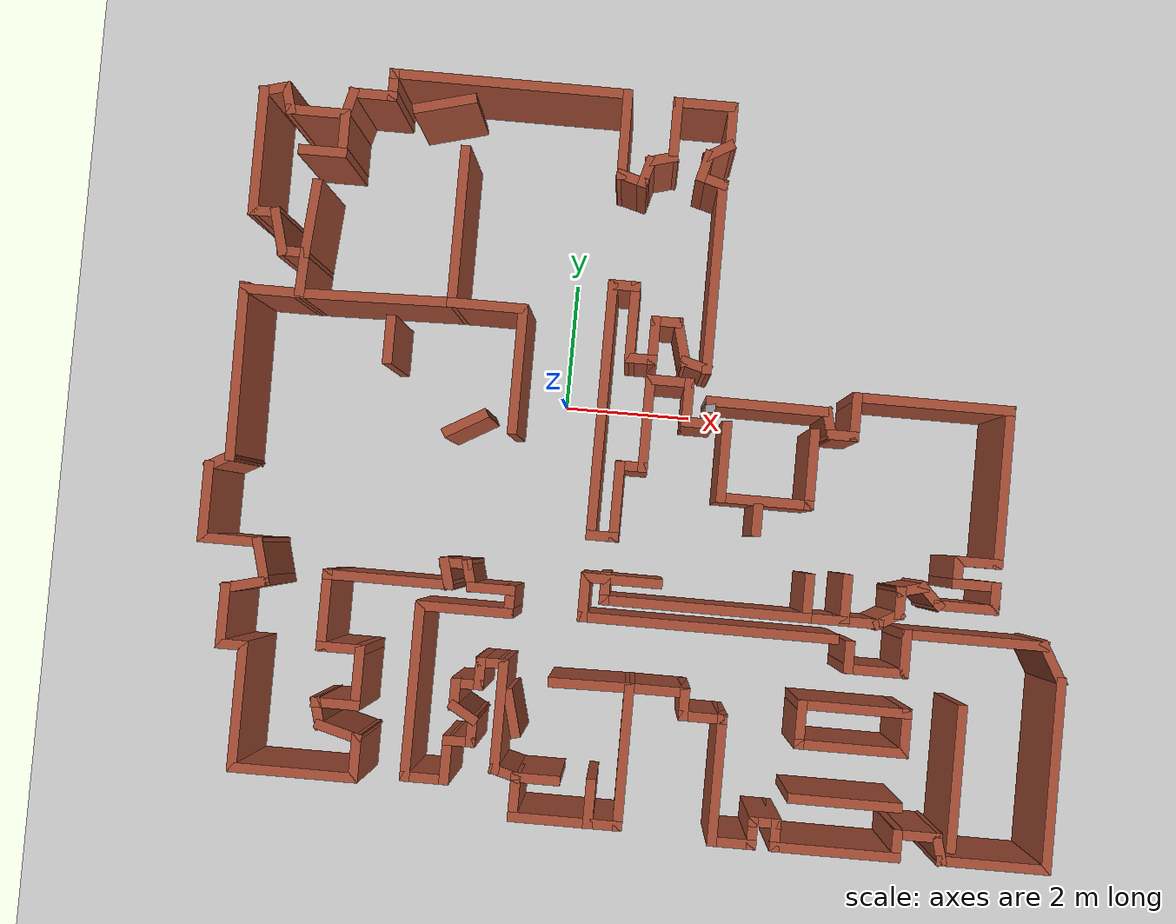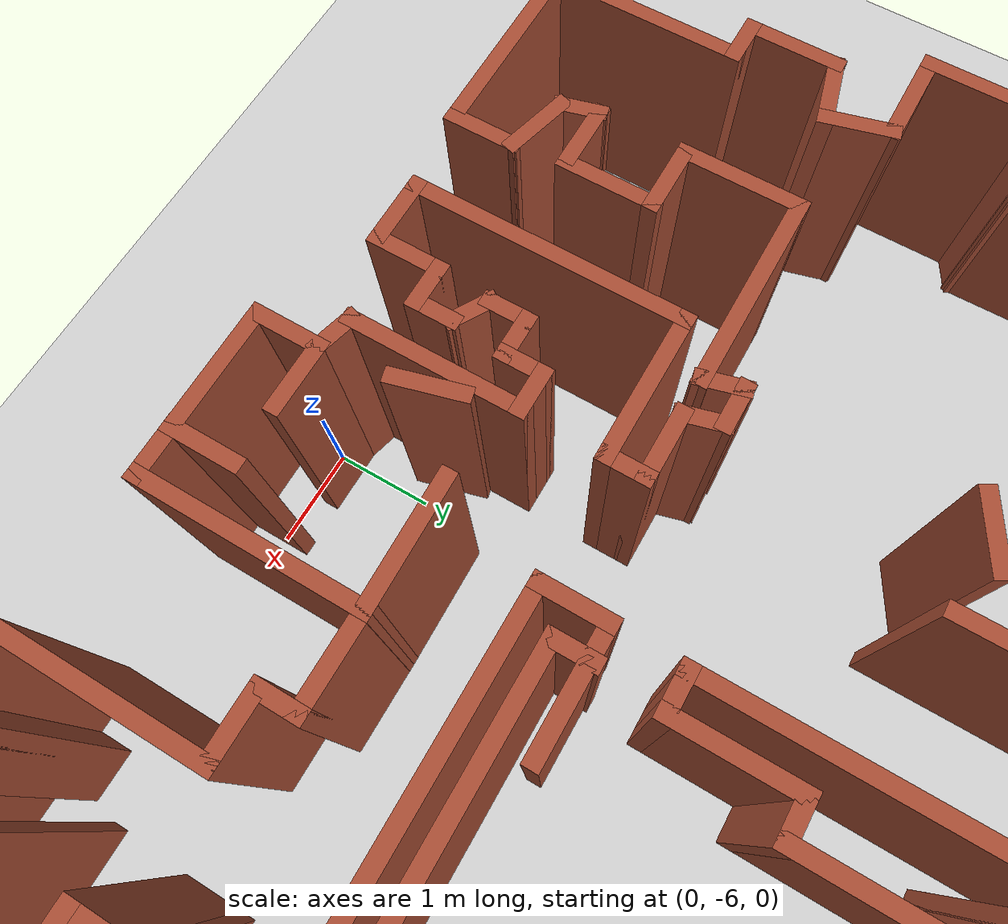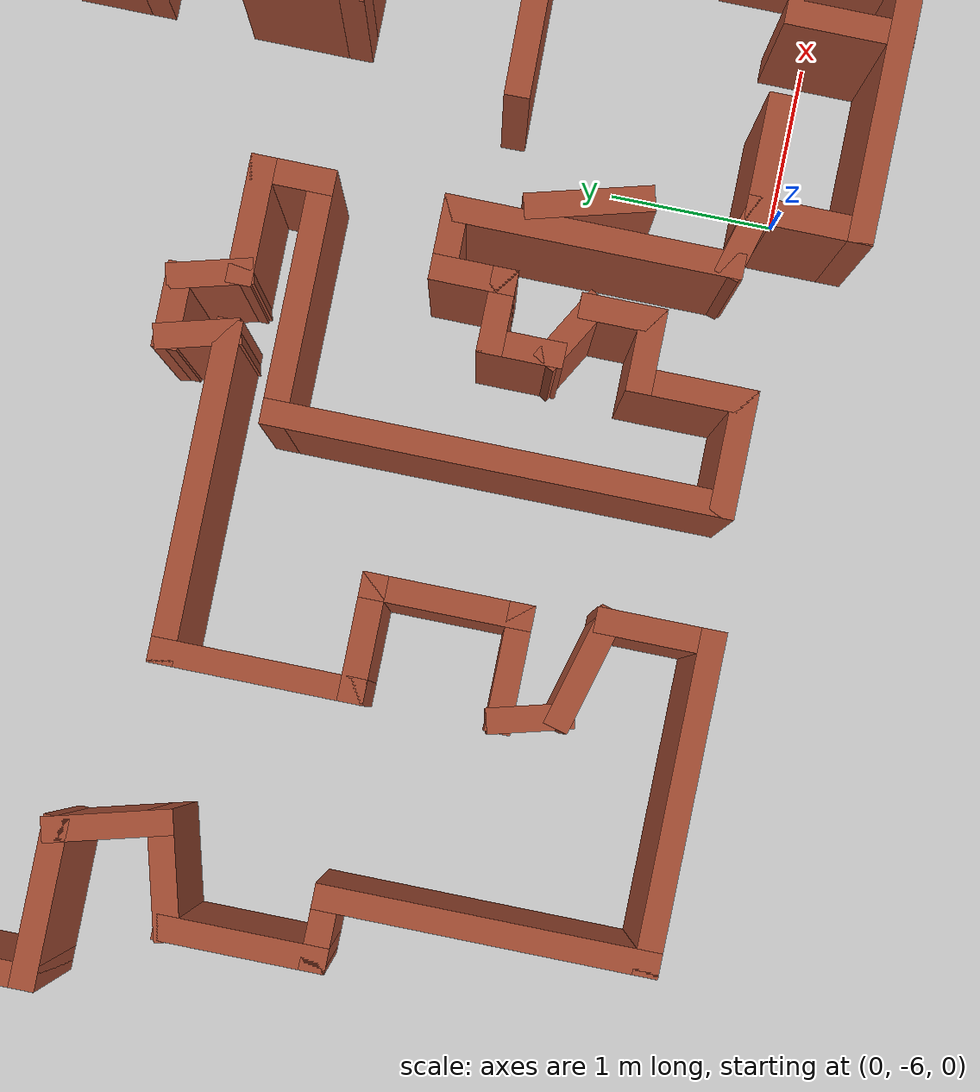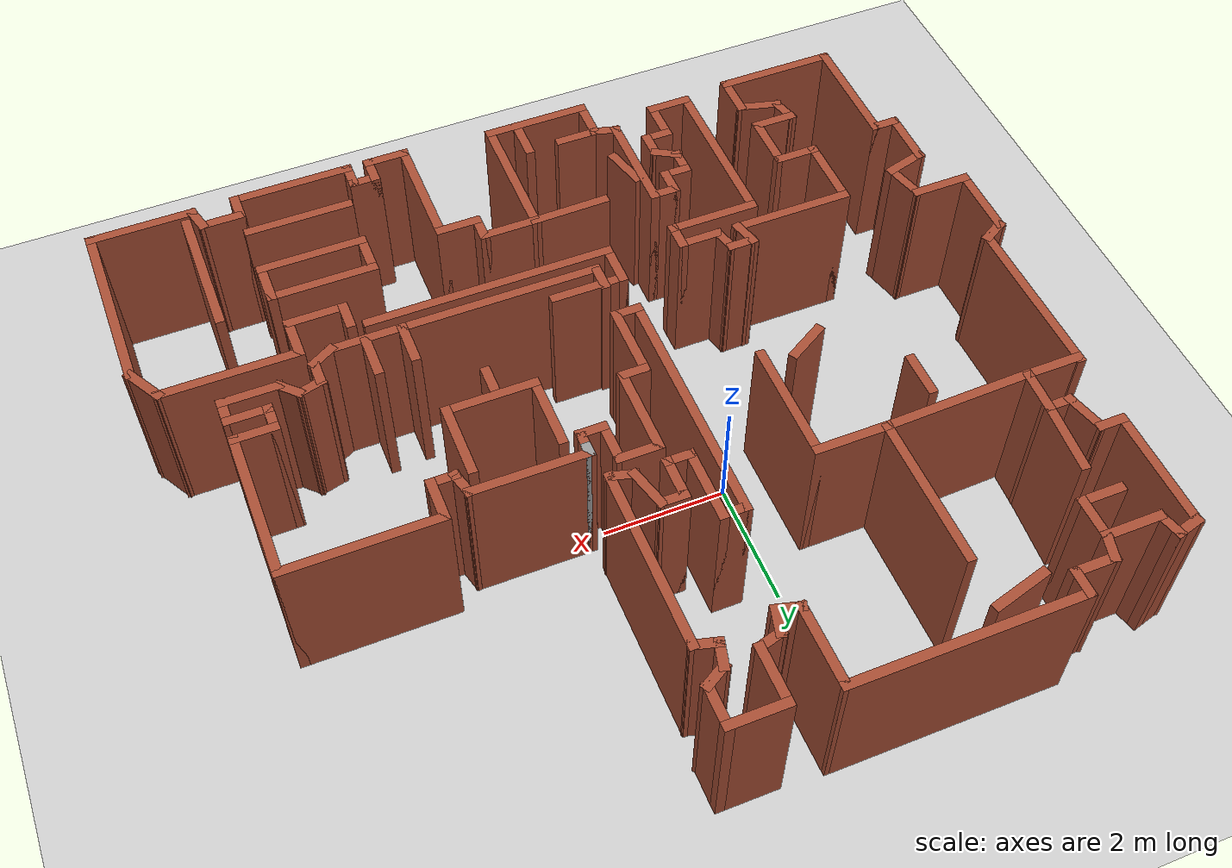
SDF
<sdf version="1.6">
 <world name="default">
  <light name="sun" type="directional">
   <pose>0 0 10 0 -0 0</pose>
   <diffuse>0.8 0.8 0.8 1</diffuse>
   <specular>0.2 0.2 0.2 1</specular>
   <attenuation>
    <range>1000</range>
    <constant>0.9</constant>
    <linear>0.01</linear>
    <quadratic>0.001</quadratic>
   </attenuation>
   <direction>-0.5 0.1 -0.9</direction>
  </light>
  <model name="ground_plane">
   <static>1</static>
   <link name="link">
    <collision name="collision">
     <geometry><plane><normal>0 0 1</normal><size>100 100</size></plane></geometry>
     <surface>
      <contact><collide_bitmask>65535</collide_bitmask></contact>
      <friction><ode><mu>100</mu><mu2>50</mu2></ode></friction>
     </surface>
    </collision>
    <visual name="visual">
     <cast_shadows>0</cast_shadows>
     <geometry><plane><normal>0 0 1</normal><size>100 100</size></plane></geometry>
     <material>
      <script><uri>file://media/materials/scripts/gazebo.material</uri><name>Gazebo/Grey</name></script>
     </material>
    </visual>
   </link>
  </model>
  <gravity>0 0 -9.8</gravity>
  <magnetic_field>6e-06 2.3e-05 -4.2e-05</magnetic_field>
  <atmosphere type="adiabatic"/>
  <physics name="default_physics" default="0" type="ode">
   <max_step_size>0.001</max_step_size>
   <real_time_factor>1</real_time_factor>
   <real_time_update_rate>1000</real_time_update_rate>
  </physics>
  <scene><ambient>0.4 0.4 0.4 1</ambient><background>0.7 0.7 0.7 1</background><shadows>1</shadows></scene>
  <audio><device>default</device></audio>
  <spherical_coordinates>
   <surface_model>EARTH_WGS84</surface_model>
   <latitude_deg>0</latitude_deg>
   <longitude_deg>0</longitude_deg>
   <elevation>0</elevation>
   <heading_deg>0</heading_deg>
  </spherical_coordinates>
  <model name="map_29">
   <pose>1.33629 -0.887991 0 0 -0 0</pose>
   <link name="Wall_0">
    <collision name="Wall_0_Collision">
     <geometry><box><size>3.75 0.15 2.5</size></box></geometry>
     <pose>0 0 1.25 0 -0 0</pose>
    </collision>
    <visual name="Wall_0_Visual">
     <pose>0 0 1.25 0 -0 0</pose>
     <geometry><box><size>3.75 0.15 2.5</size></box></geometry>
     <material>
      <script><uri>file://media/materials/scripts/gazebo.material</uri><name>Gazebo/Bricks</name></script>
      <ambient>1 1 1 1</ambient>
     </material>
     <meta><layer>0</layer></meta>
    </visual>
    <pose>-2.54851 5.6282 0 0 -0 3.14159</pose>
   </link>
   <link name="Wall_10">
    <collision name="Wall_10_Collision">
     <geometry><box><size>2 0.15 2.5</size></box></geometry>
     <pose>0 0 1.25 0 -0 0</pose>
    </collision>
    <visual name="Wall_10_Visual">
     <pose>0 0 1.25 0 -0 0</pose>
     <geometry><box><size>2 0.15 2.5</size></box></geometry>
     <material>
      <script><uri>file://media/materials/scripts/gazebo.material</uri><name>Gazebo/Bricks</name></script>
      <ambient>1 1 1 1</ambient>
     </material>
     <meta><layer>0</layer></meta>
    </visual>
    <pose>-6.31776 4.26261 0 0 -0 -1.5708</pose>
   </link>
   <link name="Wall_100">
    <collision name="Wall_100_Collision">
     <geometry><box><size>0.75 0.15 2.5</size></box></geometry>
     <pose>0 0 1.25 0 -0 0</pose>
    </collision>
    <visual name="Wall_100_Visual">
     <pose>0 0 1.25 0 -0 0</pose>
     <geometry><box><size>0.75 0.15 2.5</size></box></geometry>
     <material>
      <script><uri>file://media/materials/scripts/gazebo.material</uri><name>Gazebo/Bricks</name></script>
      <ambient>1 1 1 1</ambient>
     </material>
     <meta><layer>0</layer></meta>
    </visual>
    <pose>6.46557 -2.50228 0 0 -0 2.0944</pose>
   </link>
   <link name="Wall_101">
    <collision name="Wall_101_Collision">
     <geometry><box><size>2.25 0.15 2.5</size></box></geometry>
     <pose>0 0 1.25 0 -0 0</pose>
    </collision>
    <visual name="Wall_101_Visual">
     <pose>0 0 1.25 0 -0 0</pose>
     <geometry><box><size>2.25 0.15 2.5</size></box></geometry>
     <material>
      <script><uri>file://media/materials/scripts/gazebo.material</uri><name>Gazebo/Bricks</name></script>
      <ambient>1 1 1 1</ambient>
     </material>
     <meta><layer>0</layer></meta>
    </visual>
    <pose>5.26557 -2.24247 0 0 -0 3.14159</pose>
   </link>
   <link name="Wall_102">
    <collision name="Wall_102_Collision">
     <geometry><box><size>0.75 0.15 2.5</size></box></geometry>
     <pose>0 0 1.25 0 -0 0</pose>
    </collision>
    <visual name="Wall_102_Visual">
     <pose>0 0 1.25 0 -0 0</pose>
     <geometry><box><size>0.75 0.15 2.5</size></box></geometry>
     <material>
      <script><uri>file://media/materials/scripts/gazebo.material</uri><name>Gazebo/Bricks</name></script>
      <ambient>1 1 1 1</ambient>
     </material>
     <meta><layer>0</layer></meta>
    </visual>
    <pose>4.21557 -2.54247 0 0 -0 -1.5708</pose>
   </link>
   <link name="Wall_103">
    <collision name="Wall_103_Collision">
     <geometry><box><size>1 0.15 2.5</size></box></geometry>
     <pose>0 0 1.25 0 -0 0</pose>
    </collision>
    <visual name="Wall_103_Visual">
     <pose>0 0 1.25 0 -0 0</pose>
     <geometry><box><size>1 0.15 2.5</size></box></geometry>
     <material>
      <script><uri>file://media/materials/scripts/gazebo.material</uri><name>Gazebo/Bricks</name></script>
      <ambient>1 1 1 1</ambient>
     </material>
     <meta><layer>0</layer></meta>
    </visual>
    <pose>3.79057 -2.84247 0 0 -0 3.14159</pose>
   </link>
   <link name="Wall_104">
    <collision name="Wall_104_Collision">
     <geometry><box><size>0.5 0.15 2.5</size></box></geometry>
     <pose>0 0 1.25 0 -0 0</pose>
    </collision>
    <visual name="Wall_104_Visual">
     <pose>0 0 1.25 0 -0 0</pose>
     <geometry><box><size>0.5 0.15 2.5</size></box></geometry>
     <material>
      <script><uri>file://media/materials/scripts/gazebo.material</uri><name>Gazebo/Bricks</name></script>
      <ambient>1 1 1 1</ambient>
     </material>
     <meta><layer>0</layer></meta>
    </visual>
    <pose>3.36557 -2.66747 0 0 -0 1.5708</pose>
   </link>
   <link name="Wall_107">
    <collision name="Wall_107_Collision">
     <geometry><box><size>4 0.15 2.5</size></box></geometry>
     <pose>0 0 1.25 0 -0 0</pose>
    </collision>
    <visual name="Wall_107_Visual">
     <pose>0 0 1.25 0 -0 0</pose>
     <geometry><box><size>4 0.15 2.5</size></box></geometry>
     <material>
      <script><uri>file://media/materials/scripts/gazebo.material</uri><name>Gazebo/Bricks</name></script>
      <ambient>1 1 1 1</ambient>
     </material>
     <meta><layer>0</layer></meta>
    </visual>
    <pose>1.18819 -2.4126 0 0 -0 3.14159</pose>
   </link>
   <link name="Wall_108">
    <collision name="Wall_108_Collision">
     <geometry><box><size>0.75 0.15 2.5</size></box></geometry>
     <pose>0 0 1.25 0 -0 0</pose>
    </collision>
    <visual name="Wall_108_Visual">
     <pose>0 0 1.25 0 -0 0</pose>
     <geometry><box><size>0.75 0.15 2.5</size></box></geometry>
     <material>
      <script><uri>file://media/materials/scripts/gazebo.material</uri><name>Gazebo/Bricks</name></script>
      <ambient>1 1 1 1</ambient>
     </material>
     <meta><layer>0</layer></meta>
    </visual>
    <pose>-0.736808 -2.1126 0 0 -0 1.5708</pose>
   </link>
   <link name="Wall_109">
    <collision name="Wall_109_Collision">
     <geometry><box><size>1.25 0.15 2.5</size></box></geometry>
     <pose>0 0 1.25 0 -0 0</pose>
    </collision>
    <visual name="Wall_109_Visual">
     <pose>0 0 1.25 0 -0 0</pose>
     <geometry><box><size>1.25 0.15 2.5</size></box></geometry>
     <material>
      <script><uri>file://media/materials/scripts/gazebo.material</uri><name>Gazebo/Bricks</name></script>
      <ambient>1 1 1 1</ambient>
     </material>
     <meta><layer>0</layer></meta>
    </visual>
    <pose>-0.186808 -1.8126 0 0 -0 0</pose>
   </link>
   <link name="Wall_11">
    <collision name="Wall_11_Collision">
     <geometry><box><size>0.5 0.15 2.5</size></box></geometry>
     <pose>0 0 1.25 0 -0 0</pose>
    </collision>
    <visual name="Wall_11_Visual">
     <pose>0 0 1.25 0 -0 0</pose>
     <geometry><box><size>0.5 0.15 2.5</size></box></geometry>
     <material>
      <script><uri>file://media/materials/scripts/gazebo.material</uri><name>Gazebo/Bricks</name></script>
      <ambient>1 1 1 1</ambient>
     </material>
     <meta><layer>0</layer></meta>
    </visual>
    <pose>-6.14276 3.33761 0 0 -0 0</pose>
   </link>
   <link name="Wall_111">
    <collision name="Wall_111_Collision">
     <geometry><box><size>0.5 0.15 2.5</size></box></geometry>
     <pose>0 0 1.25 0 -0 0</pose>
    </collision>
    <visual name="Wall_111_Visual">
     <pose>0 0 1.25 0 -0 0</pose>
     <geometry><box><size>0.5 0.15 2.5</size></box></geometry>
     <material>
      <script><uri>file://media/materials/scripts/gazebo.material</uri><name>Gazebo/Bricks</name></script>
      <ambient>1 1 1 1</ambient>
     </material>
     <meta><layer>0</layer></meta>
    </visual>
    <pose>-0.431108 -1.9528 0 0 -0 -1.5708</pose>
   </link>
   <link name="Wall_112">
    <collision name="Wall_112_Collision">
     <geometry><box><size>3.25 0.15 2.5</size></box></geometry>
     <pose>0 0 1.25 0 -0 0</pose>
    </collision>
    <visual name="Wall_112_Visual">
     <pose>0 0 1.25 0 -0 0</pose>
     <geometry><box><size>3.25 0.15 2.5</size></box></geometry>
     <material>
      <script><uri>file://media/materials/scripts/gazebo.material</uri><name>Gazebo/Bricks</name></script>
      <ambient>1 1 1 1</ambient>
     </material>
     <meta><layer>0</layer></meta>
    </visual>
    <pose>1.11889 -2.1278 0 0 -0 0</pose>
   </link>
   <link name="Wall_113">
    <collision name="Wall_113_Collision">
     <geometry><box><size>0.75 0.15 2.5</size></box></geometry>
     <pose>0 0 1.25 0 -0 0</pose>
    </collision>
    <visual name="Wall_113_Visual">
     <pose>0 0 1.25 0 -0 0</pose>
     <geometry><box><size>0.75 0.15 2.5</size></box></geometry>
     <material>
      <script><uri>file://media/materials/scripts/gazebo.material</uri><name>Gazebo/Bricks</name></script>
      <ambient>1 1 1 1</ambient>
     </material>
     <meta><layer>0</layer></meta>
    </visual>
    <pose>2.66889 -1.8278 0 0 -0 1.5708</pose>
   </link>
   <link name="Wall_115">
    <collision name="Wall_115_Collision">
     <geometry><box><size>1.25 0.15 2.5</size></box></geometry>
     <pose>0 0 1.25 0 -0 0</pose>
    </collision>
    <visual name="Wall_115_Visual">
     <pose>0 0 1.25 0 -0 0</pose>
     <geometry><box><size>1.25 0.15 2.5</size></box></geometry>
     <material>
      <script><uri>file://media/materials/scripts/gazebo.material</uri><name>Gazebo/Bricks</name></script>
      <ambient>1 1 1 1</ambient>
     </material>
     <meta><layer>0</layer></meta>
    </visual>
    <pose>3.21889 -2.1278 0 0 -0 0</pose>
   </link>
   <link name="Wall_116">
    <collision name="Wall_116_Collision">
     <geometry><box><size>0.5 0.15 2.5</size></box></geometry>
     <pose>0 0 1.25 0 -0 0</pose>
    </collision>
    <visual name="Wall_116_Visual">
     <pose>0 0 1.25 0 -0 0</pose>
     <geometry><box><size>0.5 0.15 2.5</size></box></geometry>
     <material>
      <script><uri>file://media/materials/scripts/gazebo.material</uri><name>Gazebo/Bricks</name></script>
      <ambient>1 1 1 1</ambient>
     </material>
     <meta><layer>0</layer></meta>
    </visual>
    <pose>3.92045 -2.0403 0 0 -0 0.523599</pose>
   </link>
   <link name="Wall_117">
    <collision name="Wall_117_Collision">
     <geometry><box><size>0.5 0.15 2.5</size></box></geometry>
     <pose>0 0 1.25 0 -0 0</pose>
    </collision>
    <visual name="Wall_117_Visual">
     <pose>0 0 1.25 0 -0 0</pose>
     <geometry><box><size>0.5 0.15 2.5</size></box></geometry>
     <material>
      <script><uri>file://media/materials/scripts/gazebo.material</uri><name>Gazebo/Bricks</name></script>
      <ambient>1 1 1 1</ambient>
     </material>
     <meta><layer>0</layer></meta>
    </visual>
    <pose>4.072 -1.7778 0 0 -0 1.5708</pose>
   </link>
   <link name="Wall_118">
    <collision name="Wall_118_Collision">
     <geometry><box><size>0.5 0.15 2.5</size></box></geometry>
     <pose>0 0 1.25 0 -0 0</pose>
    </collision>
    <visual name="Wall_118_Visual">
     <pose>0 0 1.25 0 -0 0</pose>
     <geometry><box><size>0.5 0.15 2.5</size></box></geometry>
     <material>
      <script><uri>file://media/materials/scripts/gazebo.material</uri><name>Gazebo/Bricks</name></script>
      <ambient>1 1 1 1</ambient>
     </material>
     <meta><layer>0</layer></meta>
    </visual>
    <pose>4.24104 -1.55751 0 0 -0 0.261799</pose>
   </link>
   <link name="Wall_119">
    <collision name="Wall_119_Collision">
     <geometry><box><size>0.5 0.15 2.5</size></box></geometry>
     <pose>0 0 1.25 0 -0 0</pose>
    </collision>
    <visual name="Wall_119_Visual">
     <pose>0 0 1.25 0 -0 0</pose>
     <geometry><box><size>0.5 0.15 2.5</size></box></geometry>
     <material>
      <script><uri>file://media/materials/scripts/gazebo.material</uri><name>Gazebo/Bricks</name></script>
      <ambient>1 1 1 1</ambient>
     </material>
     <meta><layer>0</layer></meta>
    </visual>
    <pose>4.53382 -1.63596 0 0 -0 -0.785398</pose>
   </link>
   <link name="Wall_120">
    <collision name="Wall_120_Collision">
     <geometry><box><size>1 0.15 2.5</size></box></geometry>
     <pose>0 0 1.25 0 -0 0</pose>
    </collision>
    <visual name="Wall_120_Visual">
     <pose>0 0 1.25 0 -0 0</pose>
     <geometry><box><size>1 0.15 2.5</size></box></geometry>
     <material>
      <script><uri>file://media/materials/scripts/gazebo.material</uri><name>Gazebo/Bricks</name></script>
      <ambient>1 1 1 1</ambient>
     </material>
     <meta><layer>0</layer></meta>
    </visual>
    <pose>5.08256 -1.7597 0 0 -0 0</pose>
   </link>
   <link name="Wall_125">
    <collision name="Wall_125_Collision">
     <geometry><box><size>0.5 0.15 2.5</size></box></geometry>
     <pose>0 0 1.25 0 -0 0</pose>
    </collision>
    <visual name="Wall_125_Visual">
     <pose>0 0 1.25 0 -0 0</pose>
     <geometry><box><size>0.5 0.15 2.5</size></box></geometry>
     <material>
      <script><uri>file://media/materials/scripts/gazebo.material</uri><name>Gazebo/Bricks</name></script>
      <ambient>1 1 1 1</ambient>
     </material>
     <meta><layer>0</layer></meta>
    </visual>
    <pose>5.50756 -1.5847 0 0 -0 1.5708</pose>
   </link>
   <link name="Wall_126">
    <collision name="Wall_126_Collision">
     <geometry><box><size>0.75 0.15 2.5</size></box></geometry>
     <pose>0 0 1.25 0 -0 0</pose>
    </collision>
    <visual name="Wall_126_Visual">
     <pose>0 0 1.25 0 -0 0</pose>
     <geometry><box><size>0.75 0.15 2.5</size></box></geometry>
     <material>
      <script><uri>file://media/materials/scripts/gazebo.material</uri><name>Gazebo/Bricks</name></script>
      <ambient>1 1 1 1</ambient>
     </material>
     <meta><layer>0</layer></meta>
    </visual>
    <pose>5.20756 -1.4097 0 0 -0 3.14159</pose>
   </link>
   <link name="Wall_127">
    <collision name="Wall_127_Collision">
     <geometry><box><size>0.5 0.15 2.5</size></box></geometry>
     <pose>0 0 1.25 0 -0 0</pose>
    </collision>
    <visual name="Wall_127_Visual">
     <pose>0 0 1.25 0 -0 0</pose>
     <geometry><box><size>0.5 0.15 2.5</size></box></geometry>
     <material>
      <script><uri>file://media/materials/scripts/gazebo.material</uri><name>Gazebo/Bricks</name></script>
      <ambient>1 1 1 1</ambient>
     </material>
     <meta><layer>0</layer></meta>
    </visual>
    <pose>4.90756 -1.2347 0 0 -0 1.5708</pose>
   </link>
   <link name="Wall_128">
    <collision name="Wall_128_Collision">
     <geometry><box><size>0.75 0.15 2.5</size></box></geometry>
     <pose>0 0 1.25 0 -0 0</pose>
    </collision>
    <visual name="Wall_128_Visual">
     <pose>0 0 1.25 0 -0 0</pose>
     <geometry><box><size>0.75 0.15 2.5</size></box></geometry>
     <material>
      <script><uri>file://media/materials/scripts/gazebo.material</uri><name>Gazebo/Bricks</name></script>
      <ambient>1 1 1 1</ambient>
     </material>
     <meta><layer>0</layer></meta>
    </visual>
    <pose>5.20756 -1.0597 0 0 -0 0</pose>
   </link>
   <link name="Wall_129">
    <collision name="Wall_129_Collision">
     <geometry><box><size>2.5 0.15 2.5</size></box></geometry>
     <pose>0 0 1.25 0 -0 0</pose>
    </collision>
    <visual name="Wall_129_Visual">
     <pose>0 0 1.25 0 -0 0</pose>
     <geometry><box><size>2.5 0.15 2.5</size></box></geometry>
     <material>
      <script><uri>file://media/materials/scripts/gazebo.material</uri><name>Gazebo/Bricks</name></script>
      <ambient>1 1 1 1</ambient>
     </material>
     <meta><layer>0</layer></meta>
    </visual>
    <pose>5.50756 0.115297 0 0 -0 1.5708</pose>
   </link>
   <link name="Wall_130">
    <collision name="Wall_130_Collision">
     <geometry><box><size>2.5 0.15 2.5</size></box></geometry>
     <pose>0 0 1.25 0 -0 0</pose>
    </collision>
    <visual name="Wall_130_Visual">
     <pose>0 0 1.25 0 -0 0</pose>
     <geometry><box><size>2.5 0.15 2.5</size></box></geometry>
     <material>
      <script><uri>file://media/materials/scripts/gazebo.material</uri><name>Gazebo/Bricks</name></script>
      <ambient>1 1 1 1</ambient>
     </material>
     <meta><layer>0</layer></meta>
    </visual>
    <pose>4.33256 1.2903 0 0 -0 3.14159</pose>
   </link>
   <link name="Wall_135">
    <collision name="Wall_135_Collision">
     <geometry><box><size>0.25 0.15 2.5</size></box></geometry>
     <pose>0 0 1.25 0 -0 0</pose>
    </collision>
    <visual name="Wall_135_Visual">
     <pose>0 0 1.25 0 -0 0</pose>
     <geometry><box><size>0.25 0.15 2.5</size></box></geometry>
     <material>
      <script><uri>file://media/materials/scripts/gazebo.material</uri><name>Gazebo/Grey</name></script>
      <ambient>1 1 1 1</ambient>
     </material>
     <meta><layer>0</layer></meta>
    </visual>
    <pose>0.931681 0.98689 0 0 -0 -1.5708</pose>
   </link>
   <link name="Wall_139">
    <collision name="Wall_139_Collision">
     <geometry><box><size>0.75 0.15 2.5</size></box></geometry>
     <pose>0 0 1.25 0 -0 0</pose>
    </collision>
    <visual name="Wall_139_Visual">
     <pose>0 0 1.25 0 -0 0</pose>
     <geometry><box><size>0.75 0.15 2.5</size></box></geometry>
     <material>
      <script><uri>file://media/materials/scripts/gazebo.material</uri><name>Gazebo/Bricks</name></script>
      <ambient>1 1 1 1</ambient>
     </material>
     <meta><layer>0</layer></meta>
    </visual>
    <pose>3.15756 0.990297 0 0 -0 -1.5708</pose>
   </link>
   <link name="Wall_140">
    <collision name="Wall_140_Collision">
     <geometry><box><size>0.5 0.15 2.5</size></box></geometry>
     <pose>0 0 1.25 0 -0 0</pose>
    </collision>
    <visual name="Wall_140_Visual">
     <pose>0 0 1.25 0 -0 0</pose>
     <geometry><box><size>0.5 0.15 2.5</size></box></geometry>
     <material>
      <script><uri>file://media/materials/scripts/gazebo.material</uri><name>Gazebo/Bricks</name></script>
      <ambient>1 1 1 1</ambient>
     </material>
     <meta><layer>0</layer></meta>
    </visual>
    <pose>2.98256 0.690297 0 0 -0 3.14159</pose>
   </link>
   <link name="Wall_141">
    <collision name="Wall_141_Collision">
     <geometry><box><size>0.5 0.15 2.5</size></box></geometry>
     <pose>0 0 1.25 0 -0 0</pose>
    </collision>
    <visual name="Wall_141_Visual">
     <pose>0 0 1.25 0 -0 0</pose>
     <geometry><box><size>0.5 0.15 2.5</size></box></geometry>
     <material>
      <script><uri>file://media/materials/scripts/gazebo.material</uri><name>Gazebo/Bricks</name></script>
      <ambient>1 1 1 1</ambient>
     </material>
     <meta><layer>0</layer></meta>
    </visual>
    <pose>2.76227 0.859334 0 0 -0 1.8326</pose>
   </link>
   <link name="Wall_142">
    <collision name="Wall_142_Collision">
     <geometry><box><size>1.93532 0.15 2.5</size></box></geometry>
     <pose>0 0 1.25 0 -0 0</pose>
    </collision>
    <visual name="Wall_142_Visual">
     <pose>0 0 1.25 0 -0 0</pose>
     <geometry><box><size>1.93532 0.15 2.5</size></box></geometry>
     <material>
      <script><uri>file://media/materials/scripts/gazebo.material</uri><name>Gazebo/Bricks</name></script>
      <ambient>1 1 1 1</ambient>
     </material>
     <meta><layer>0</layer></meta>
    </visual>
    <pose>1.82433 1.03263 0 0 -0 3.13682</pose>
   </link>
   <link name="Wall_145">
    <collision name="Wall_145_Collision">
     <geometry><box><size>0.5 0.15 2.5</size></box></geometry>
     <pose>0 0 1.25 0 -0 0</pose>
    </collision>
    <visual name="Wall_145_Visual">
     <pose>0 0 1.25 0 -0 0</pose>
     <geometry><box><size>0.5 0.15 2.5</size></box></geometry>
     <material>
      <script><uri>file://media/materials/scripts/gazebo.material</uri><name>Gazebo/Bricks</name></script>
      <ambient>1 1 1 1</ambient>
     </material>
     <meta><layer>0</layer></meta>
    </visual>
    <pose>0.931681 0.86189 0 0 -0 -1.5708</pose>
   </link>
   <link name="Wall_146">
    <collision name="Wall_146_Collision">
     <geometry><box><size>0.5 0.15 2.5</size></box></geometry>
     <pose>0 0 1.25 0 -0 0</pose>
    </collision>
    <visual name="Wall_146_Visual">
     <pose>0 0 1.25 0 -0 0</pose>
     <geometry><box><size>0.5 0.15 2.5</size></box></geometry>
     <material>
      <script><uri>file://media/materials/scripts/gazebo.material</uri><name>Gazebo/Bricks</name></script>
      <ambient>1 1 1 1</ambient>
     </material>
     <meta><layer>0</layer></meta>
    </visual>
    <pose>0.756681 0.686889 0 0 -0 3.14159</pose>
   </link>
   <link name="Wall_149">
    <collision name="Wall_149_Collision">
     <geometry><box><size>0.75 0.15 2.5</size></box></geometry>
     <pose>0 0 1.25 0 -0 0</pose>
    </collision>
    <visual name="Wall_149_Visual">
     <pose>0 0 1.25 0 -0 0</pose>
     <geometry><box><size>0.75 0.15 2.5</size></box></geometry>
     <material>
      <script><uri>file://media/materials/scripts/gazebo.material</uri><name>Gazebo/Bricks</name></script>
      <ambient>1 1 1 1</ambient>
     </material>
     <meta><layer>0</layer></meta>
    </visual>
    <pose>0.581681 0.98689 0 0 -0 1.5708</pose>
   </link>
   <link name="Wall_15">
    <collision name="Wall_15_Collision">
     <geometry><box><size>0.75 0.15 2.5</size></box></geometry>
     <pose>0 0 1.25 0 -0 0</pose>
    </collision>
    <visual name="Wall_15_Visual">
     <pose>0 0 1.25 0 -0 0</pose>
     <geometry><box><size>0.75 0.15 2.5</size></box></geometry>
     <material>
      <script><uri>file://media/materials/scripts/gazebo.material</uri><name>Gazebo/Bricks</name></script>
      <ambient>1 1 1 1</ambient>
     </material>
     <meta><layer>0</layer></meta>
    </visual>
    <pose>-5.89011 3.04783 0 0 -0 -1.309</pose>
   </link>
   <link name="Wall_150">
    <collision name="Wall_150_Collision">
     <geometry><box><size>0.75 0.15 2.5</size></box></geometry>
     <pose>0 0 1.25 0 -0 0</pose>
    </collision>
    <visual name="Wall_150_Visual">
     <pose>0 0 1.25 0 -0 0</pose>
     <geometry><box><size>0.75 0.15 2.5</size></box></geometry>
     <material>
      <script><uri>file://media/materials/scripts/gazebo.material</uri><name>Gazebo/Bricks</name></script>
      <ambient>1 1 1 1</ambient>
     </material>
     <meta><layer>0</layer></meta>
    </visual>
    <pose>0.281681 1.28689 0 0 -0 3.14159</pose>
   </link>
   <link name="Wall_151">
    <collision name="Wall_151_Collision">
     <geometry><box><size>1.5 0.15 2.5</size></box></geometry>
     <pose>0 0 1.25 0 -0 0</pose>
    </collision>
    <visual name="Wall_151_Visual">
     <pose>0 0 1.25 0 -0 0</pose>
     <geometry><box><size>1.5 0.15 2.5</size></box></geometry>
     <material>
      <script><uri>file://media/materials/scripts/gazebo.material</uri><name>Gazebo/Bricks</name></script>
      <ambient>1 1 1 1</ambient>
     </material>
     <meta><layer>0</layer></meta>
    </visual>
    <pose>-0.018319 0.61189 0 0 -0 -1.5708</pose>
   </link>
   <link name="Wall_152">
    <collision name="Wall_152_Collision">
     <geometry><box><size>0.5 0.15 2.5</size></box></geometry>
     <pose>0 0 1.25 0 -0 0</pose>
    </collision>
    <visual name="Wall_152_Visual">
     <pose>0 0 1.25 0 -0 0</pose>
     <geometry><box><size>0.5 0.15 2.5</size></box></geometry>
     <material>
      <script><uri>file://media/materials/scripts/gazebo.material</uri><name>Gazebo/Bricks</name></script>
      <ambient>1 1 1 1</ambient>
     </material>
     <meta><layer>0</layer></meta>
    </visual>
    <pose>-0.193319 -0.06311 0 0 -0 3.14159</pose>
   </link>
   <link name="Wall_153">
    <collision name="Wall_153_Collision">
     <geometry><box><size>1.25 0.15 2.5</size></box></geometry>
     <pose>0 0 1.25 0 -0 0</pose>
    </collision>
    <visual name="Wall_153_Visual">
     <pose>0 0 1.25 0 -0 0</pose>
     <geometry><box><size>1.25 0.15 2.5</size></box></geometry>
     <material>
      <script><uri>file://media/materials/scripts/gazebo.material</uri><name>Gazebo/Bricks</name></script>
      <ambient>1 1 1 1</ambient>
     </material>
     <meta><layer>0</layer></meta>
    </visual>
    <pose>-0.368319 -0.613111 0 0 -0 -1.5708</pose>
   </link>
   <link name="Wall_154">
    <collision name="Wall_154_Collision">
     <geometry><box><size>0.5 0.15 2.5</size></box></geometry>
     <pose>0 0 1.25 0 -0 0</pose>
    </collision>
    <visual name="Wall_154_Visual">
     <pose>0 0 1.25 0 -0 0</pose>
     <geometry><box><size>0.5 0.15 2.5</size></box></geometry>
     <material>
      <script><uri>file://media/materials/scripts/gazebo.material</uri><name>Gazebo/Bricks</name></script>
      <ambient>1 1 1 1</ambient>
     </material>
     <meta><layer>0</layer></meta>
    </visual>
    <pose>-0.543319 -1.16311 0 0 -0 3.14159</pose>
   </link>
   <link name="Wall_155">
    <collision name="Wall_155_Collision">
     <geometry><box><size>4 0.15 2.5</size></box></geometry>
     <pose>0 0 1.25 0 -0 0</pose>
    </collision>
    <visual name="Wall_155_Visual">
     <pose>0 0 1.25 0 -0 0</pose>
     <geometry><box><size>4 0.15 2.5</size></box></geometry>
     <material>
      <script><uri>file://media/materials/scripts/gazebo.material</uri><name>Gazebo/Bricks</name></script>
      <ambient>1 1 1 1</ambient>
     </material>
     <meta><layer>0</layer></meta>
    </visual>
    <pose>-0.718319 0.761889 0 0 -0 1.5708</pose>
   </link>
   <link name="Wall_156">
    <collision name="Wall_156_Collision">
     <geometry><box><size>0.5 0.15 2.5</size></box></geometry>
     <pose>0 0 1.25 0 -0 0</pose>
    </collision>
    <visual name="Wall_156_Visual">
     <pose>0 0 1.25 0 -0 0</pose>
     <geometry><box><size>0.5 0.15 2.5</size></box></geometry>
     <material>
      <script><uri>file://media/materials/scripts/gazebo.material</uri><name>Gazebo/Bricks</name></script>
      <ambient>1 1 1 1</ambient>
     </material>
     <meta><layer>0</layer></meta>
    </visual>
    <pose>-0.543319 2.68689 0 0 -0 0</pose>
   </link>
   <link name="Wall_157">
    <collision name="Wall_157_Collision">
     <geometry><box><size>1.25 0.15 2.5</size></box></geometry>
     <pose>0 0 1.25 0 -0 0</pose>
    </collision>
    <visual name="Wall_157_Visual">
     <pose>0 0 1.25 0 -0 0</pose>
     <geometry><box><size>1.25 0.15 2.5</size></box></geometry>
     <material>
      <script><uri>file://media/materials/scripts/gazebo.material</uri><name>Gazebo/Bricks</name></script>
      <ambient>1 1 1 1</ambient>
     </material>
     <meta><layer>0</layer></meta>
    </visual>
    <pose>-0.368319 2.13689 0 0 -0 -1.5708</pose>
   </link>
   <link name="Wall_158">
    <collision name="Wall_158_Collision">
     <geometry><box><size>0.5 0.15 2.5</size></box></geometry>
     <pose>0 0 1.25 0 -0 0</pose>
    </collision>
    <visual name="Wall_158_Visual">
     <pose>0 0 1.25 0 -0 0</pose>
     <geometry><box><size>0.5 0.15 2.5</size></box></geometry>
     <material>
      <script><uri>file://media/materials/scripts/gazebo.material</uri><name>Gazebo/Bricks</name></script>
      <ambient>1 1 1 1</ambient>
     </material>
     <meta><layer>0</layer></meta>
    </visual>
    <pose>-0.193319 1.58689 0 0 -0 0</pose>
   </link>
   <link name="Wall_159">
    <collision name="Wall_159_Collision">
     <geometry><box><size>0.75 0.15 2.5</size></box></geometry>
     <pose>0 0 1.25 0 -0 0</pose>
    </collision>
    <visual name="Wall_159_Visual">
     <pose>0 0 1.25 0 -0 0</pose>
     <geometry><box><size>0.75 0.15 2.5</size></box></geometry>
     <material>
      <script><uri>file://media/materials/scripts/gazebo.material</uri><name>Gazebo/Bricks</name></script>
      <ambient>1 1 1 1</ambient>
     </material>
     <meta><layer>0</layer></meta>
    </visual>
    <pose>-0.018319 1.88689 0 0 -0 1.5708</pose>
   </link>
   <link name="Wall_16">
    <collision name="Wall_16_Collision">
     <geometry><box><size>0.5 0.15 2.5</size></box></geometry>
     <pose>0 0 1.25 0 -0 0</pose>
    </collision>
    <visual name="Wall_16_Visual">
     <pose>0 0 1.25 0 -0 0</pose>
     <geometry><box><size>0.5 0.15 2.5</size></box></geometry>
     <material>
      <script><uri>file://media/materials/scripts/gazebo.material</uri><name>Gazebo/Bricks</name></script>
      <ambient>1 1 1 1</ambient>
     </material>
     <meta><layer>0</layer></meta>
    </visual>
    <pose>-5.63746 2.75806 0 0 -0 0</pose>
   </link>
   <link name="Wall_160">
    <collision name="Wall_160_Collision">
     <geometry><box><size>0.5 0.15 2.5</size></box></geometry>
     <pose>0 0 1.25 0 -0 0</pose>
    </collision>
    <visual name="Wall_160_Visual">
     <pose>0 0 1.25 0 -0 0</pose>
     <geometry><box><size>0.5 0.15 2.5</size></box></geometry>
     <material>
      <script><uri>file://media/materials/scripts/gazebo.material</uri><name>Gazebo/Bricks</name></script>
      <ambient>1 1 1 1</ambient>
     </material>
     <meta><layer>0</layer></meta>
    </visual>
    <pose>0.156681 2.18689 0 0 -0 0</pose>
   </link>
   <link name="Wall_161">
    <collision name="Wall_161_Collision">
     <geometry><box><size>0.75 0.15 2.5</size></box></geometry>
     <pose>0 0 1.25 0 -0 0</pose>
    </collision>
    <visual name="Wall_161_Visual">
     <pose>0 0 1.25 0 -0 0</pose>
     <geometry><box><size>0.75 0.15 2.5</size></box></geometry>
     <material>
      <script><uri>file://media/materials/scripts/gazebo.material</uri><name>Gazebo/Bricks</name></script>
      <ambient>1 1 1 1</ambient>
     </material>
     <meta><layer>0</layer></meta>
    </visual>
    <pose>0.409326 1.89711 0 0 -0 -1.309</pose>
   </link>
   <link name="Wall_162">
    <collision name="Wall_162_Collision">
     <geometry><box><size>0.5 0.15 2.5</size></box></geometry>
     <pose>0 0 1.25 0 -0 0</pose>
    </collision>
    <visual name="Wall_162_Visual">
     <pose>0 0 1.25 0 -0 0</pose>
     <geometry><box><size>0.5 0.15 2.5</size></box></geometry>
     <material>
      <script><uri>file://media/materials/scripts/gazebo.material</uri><name>Gazebo/Bricks</name></script>
      <ambient>1 1 1 1</ambient>
     </material>
     <meta><layer>0</layer></meta>
    </visual>
    <pose>0.656009 1.56204 0 0 -0 -0.261799</pose>
   </link>
   <link name="Wall_165">
    <collision name="Wall_165_Collision">
     <geometry><box><size>3 0.15 2.5</size></box></geometry>
     <pose>0 0 1.25 0 -0 0</pose>
    </collision>
    <visual name="Wall_165_Visual">
     <pose>0 0 1.25 0 -0 0</pose>
     <geometry><box><size>3 0.15 2.5</size></box></geometry>
     <material>
      <script><uri>file://media/materials/scripts/gazebo.material</uri><name>Gazebo/Bricks</name></script>
      <ambient>1 1 1 1</ambient>
     </material>
     <meta><layer>0</layer></meta>
    </visual>
    <pose>0.825046 2.94175 0 0 -0 1.5708</pose>
   </link>
   <link name="Wall_166">
    <collision name="Wall_166_Collision">
     <geometry><box><size>0.5 0.15 2.5</size></box></geometry>
     <pose>0 0 1.25 0 -0 0</pose>
    </collision>
    <visual name="Wall_166_Visual">
     <pose>0 0 1.25 0 -0 0</pose>
     <geometry><box><size>0.5 0.15 2.5</size></box></geometry>
     <material>
      <script><uri>file://media/materials/scripts/gazebo.material</uri><name>Gazebo/Bricks</name></script>
      <ambient>1 1 1 1</ambient>
     </material>
     <meta><layer>0</layer></meta>
    </visual>
    <pose>0.656009 4.41204 0 0 -0 2.87979</pose>
   </link>
   <link name="Wall_167">
    <collision name="Wall_167_Collision">
     <geometry><box><size>0.5 0.15 2.5</size></box></geometry>
     <pose>0 0 1.25 0 -0 0</pose>
    </collision>
    <visual name="Wall_167_Visual">
     <pose>0 0 1.25 0 -0 0</pose>
     <geometry><box><size>0.5 0.15 2.5</size></box></geometry>
     <material>
      <script><uri>file://media/materials/scripts/gazebo.material</uri><name>Gazebo/Bricks</name></script>
      <ambient>1 1 1 1</ambient>
     </material>
     <meta><layer>0</layer></meta>
    </visual>
    <pose>0.532265 4.62637 0 0 -0 1.309</pose>
   </link>
   <link name="Wall_168">
    <collision name="Wall_168_Collision">
     <geometry><box><size>0.5 0.15 2.5</size></box></geometry>
     <pose>0 0 1.25 0 -0 0</pose>
    </collision>
    <visual name="Wall_168_Visual">
     <pose>0 0 1.25 0 -0 0</pose>
     <geometry><box><size>0.5 0.15 2.5</size></box></geometry>
     <material>
      <script><uri>file://media/materials/scripts/gazebo.material</uri><name>Gazebo/Bricks</name></script>
      <ambient>1 1 1 1</ambient>
     </material>
     <meta><layer>0</layer></meta>
    </visual>
    <pose>0.729113 4.88291 0 0 -0 0.523599</pose>
   </link>
   <link name="Wall_169">
    <collision name="Wall_169_Collision">
     <geometry><box><size>0.75 0.15 2.5</size></box></geometry>
     <pose>0 0 1.25 0 -0 0</pose>
    </collision>
    <visual name="Wall_169_Visual">
     <pose>0 0 1.25 0 -0 0</pose>
     <geometry><box><size>0.75 0.15 2.5</size></box></geometry>
     <material>
      <script><uri>file://media/materials/scripts/gazebo.material</uri><name>Gazebo/Bricks</name></script>
      <ambient>1 1 1 1</ambient>
     </material>
     <meta><layer>0</layer></meta>
    </visual>
    <pose>0.880668 5.27041 0 0 -0 1.5708</pose>
   </link>
   <link name="Wall_17">
    <collision name="Wall_17_Collision">
     <geometry><box><size>0.750583 0.15 2.5</size></box></geometry>
     <pose>0 0 1.25 0 -0 0</pose>
    </collision>
    <visual name="Wall_17_Visual">
     <pose>0 0 1.25 0 -0 0</pose>
     <geometry><box><size>0.750583 0.15 2.5</size></box></geometry>
     <material>
      <script><uri>file://media/materials/scripts/gazebo.material</uri><name>Gazebo/Bricks</name></script>
      <ambient>1 1 1 1</ambient>
     </material>
     <meta><layer>0</layer></meta>
    </visual>
    <pose>-5.47569 2.45805 0 0 -0 -1.61485</pose>
   </link>
   <link name="Wall_170">
    <collision name="Wall_170_Collision">
     <geometry><box><size>1 0.15 2.5</size></box></geometry>
     <pose>0 0 1.25 0 -0 0</pose>
    </collision>
    <visual name="Wall_170_Visual">
     <pose>0 0 1.25 0 -0 0</pose>
     <geometry><box><size>1 0.15 2.5</size></box></geometry>
     <material>
      <script><uri>file://media/materials/scripts/gazebo.material</uri><name>Gazebo/Bricks</name></script>
      <ambient>1 1 1 1</ambient>
     </material>
     <meta><layer>0</layer></meta>
    </visual>
    <pose>0.455668 5.57041 0 0 -0 3.14159</pose>
   </link>
   <link name="Wall_171">
    <collision name="Wall_171_Collision">
     <geometry><box><size>1 0.15 2.5</size></box></geometry>
     <pose>0 0 1.25 0 -0 0</pose>
    </collision>
    <visual name="Wall_171_Visual">
     <pose>0 0 1.25 0 -0 0</pose>
     <geometry><box><size>1 0.15 2.5</size></box></geometry>
     <material>
      <script><uri>file://media/materials/scripts/gazebo.material</uri><name>Gazebo/Bricks</name></script>
      <ambient>1 1 1 1</ambient>
     </material>
     <meta><layer>0</layer></meta>
    </visual>
    <pose>0.030668 5.14541 0 0 -0 -1.5708</pose>
   </link>
   <link name="Wall_173">
    <collision name="Wall_173_Collision">
     <geometry><box><size>0.5 0.15 2.5</size></box></geometry>
     <pose>0 0 1.25 0 -0 0</pose>
    </collision>
    <visual name="Wall_173_Visual">
     <pose>0 0 1.25 0 -0 0</pose>
     <geometry><box><size>0.5 0.15 2.5</size></box></geometry>
     <material>
      <script><uri>file://media/materials/scripts/gazebo.material</uri><name>Gazebo/Bricks</name></script>
      <ambient>1 1 1 1</ambient>
     </material>
     <meta><layer>0</layer></meta>
    </visual>
    <pose>-0.138369 4.67511 0 0 -0 -2.87979</pose>
   </link>
   <link name="Wall_174">
    <collision name="Wall_174_Collision">
     <geometry><box><size>0.5 0.15 2.5</size></box></geometry>
     <pose>0 0 1.25 0 -0 0</pose>
    </collision>
    <visual name="Wall_174_Visual">
     <pose>0 0 1.25 0 -0 0</pose>
     <geometry><box><size>0.5 0.15 2.5</size></box></geometry>
     <material>
      <script><uri>file://media/materials/scripts/gazebo.material</uri><name>Gazebo/Bricks</name></script>
      <ambient>1 1 1 1</ambient>
     </material>
     <meta><layer>0</layer></meta>
    </visual>
    <pose>-0.3527 4.46078 0 0 -0 -1.8326</pose>
   </link>
   <link name="Wall_175">
    <collision name="Wall_175_Collision">
     <geometry><box><size>0.5 0.15 2.5</size></box></geometry>
     <pose>0 0 1.25 0 -0 0</pose>
    </collision>
    <visual name="Wall_175_Visual">
     <pose>0 0 1.25 0 -0 0</pose>
     <geometry><box><size>0.5 0.15 2.5</size></box></geometry>
     <material>
      <script><uri>file://media/materials/scripts/gazebo.material</uri><name>Gazebo/Bricks</name></script>
      <ambient>1 1 1 1</ambient>
     </material>
     <meta><layer>0</layer></meta>
    </visual>
    <pose>-0.56703 4.33704 0 0 -0 2.87979</pose>
   </link>
   <link name="Wall_176">
    <collision name="Wall_176_Collision">
     <geometry><box><size>1.39593 0.15 2.5</size></box></geometry>
     <pose>0 0 1.25 0 -0 0</pose>
    </collision>
    <visual name="Wall_176_Visual">
     <pose>0 0 1.25 0 -0 0</pose>
     <geometry><box><size>1.39593 0.15 2.5</size></box></geometry>
     <material>
      <script><uri>file://media/materials/scripts/gazebo.material</uri><name>Gazebo/Bricks</name></script>
      <ambient>1 1 1 1</ambient>
     </material>
     <meta><layer>0</layer></meta>
    </visual>
    <pose>-0.742287 5.00527 0 0 -0 1.58078</pose>
   </link>
   <link name="Wall_178">
    <collision name="Wall_178_Collision">
     <geometry><box><size>1 0.15 2.5</size></box></geometry>
     <pose>0 0 1.25 0 -0 0</pose>
    </collision>
    <visual name="Wall_178_Visual">
     <pose>0 0 1.25 0 -0 0</pose>
     <geometry><box><size>1 0.15 2.5</size></box></geometry>
     <material>
      <script><uri>file://media/materials/scripts/gazebo.material</uri><name>Gazebo/Bricks</name></script>
      <ambient>1 1 1 1</ambient>
     </material>
     <meta><layer>0</layer></meta>
    </visual>
    <pose>-3.53844 5.23565 0 0 -0 0.261799</pose>
   </link>
   <link name="Wall_180">
    <collision name="Wall_180_Collision">
     <geometry><box><size>2.5 0.15 2.5</size></box></geometry>
     <pose>0 0 1.25 0 -0 0</pose>
    </collision>
    <visual name="Wall_180_Visual">
     <pose>0 0 1.25 0 -0 0</pose>
     <geometry><box><size>2.5 0.15 2.5</size></box></geometry>
     <material>
      <script><uri>file://media/materials/scripts/gazebo.material</uri><name>Gazebo/Bricks</name></script>
      <ambient>1 1 1 1</ambient>
     </material>
     <meta><layer>0</layer></meta>
    </visual>
    <pose>-3.15546 3.36875 0 0 -0 -1.5708</pose>
   </link>
   <link name="Wall_182">
    <collision name="Wall_182_Collision">
     <geometry><box><size>1.22492 0.15 2.5</size></box></geometry>
     <pose>0 0 1.25 0 -0 0</pose>
    </collision>
    <visual name="Wall_182_Visual">
     <pose>0 0 1.25 0 -0 0</pose>
     <geometry><box><size>1.22492 0.15 2.5</size></box></geometry>
     <material>
      <script><uri>file://media/materials/scripts/gazebo.material</uri><name>Gazebo/Bricks</name></script>
      <ambient>1 1 1 1</ambient>
     </material>
     <meta><layer>0</layer></meta>
    </visual>
    <pose>-5.41986 3.29383 0 0 -0 -1.65015</pose>
   </link>
   <link name="Wall_184">
    <collision name="Wall_184_Collision">
     <geometry><box><size>0.75 0.15 2.5</size></box></geometry>
     <pose>0 0 1.25 0 -0 0</pose>
    </collision>
    <visual name="Wall_184_Visual">
     <pose>0 0 1.25 0 -0 0</pose>
     <geometry><box><size>0.75 0.15 2.5</size></box></geometry>
     <material>
      <script><uri>file://media/materials/scripts/gazebo.material</uri><name>Gazebo/Bricks</name></script>
      <ambient>1 1 1 1</ambient>
     </material>
     <meta><layer>0</layer></meta>
    </visual>
    <pose>-5.03909 4.64012 0 0 -0 -1.5708</pose>
   </link>
   <link name="Wall_185">
    <collision name="Wall_185_Collision">
     <geometry><box><size>0.75 0.15 2.5</size></box></geometry>
     <pose>0 0 1.25 0 -0 0</pose>
    </collision>
    <visual name="Wall_185_Visual">
     <pose>0 0 1.25 0 -0 0</pose>
     <geometry><box><size>0.75 0.15 2.5</size></box></geometry>
     <material>
      <script><uri>file://media/materials/scripts/gazebo.material</uri><name>Gazebo/Bricks</name></script>
      <ambient>1 1 1 1</ambient>
     </material>
     <meta><layer>0</layer></meta>
    </visual>
    <pose>-5.33909 4.34012 0 0 -0 3.14159</pose>
   </link>
   <link name="Wall_187">
    <collision name="Wall_187_Collision">
     <geometry><box><size>0.75 0.15 2.5</size></box></geometry>
     <pose>0 0 1.25 0 -0 0</pose>
    </collision>
    <visual name="Wall_187_Visual">
     <pose>0 0 1.25 0 -0 0</pose>
     <geometry><box><size>0.75 0.15 2.5</size></box></geometry>
     <material>
      <script><uri>file://media/materials/scripts/gazebo.material</uri><name>Gazebo/Bricks</name></script>
      <ambient>1 1 1 1</ambient>
     </material>
     <meta><layer>0</layer></meta>
    </visual>
    <pose>-4.05476 1.54585 0 0 -0 -1.5708</pose>
   </link>
   <link name="Wall_190">
    <collision name="Wall_190_Collision">
     <geometry><box><size>2.48428 0.15 2.5</size></box></geometry>
     <pose>0 0 1.25 0 -0 0</pose>
    </collision>
    <visual name="Wall_190_Visual">
     <pose>0 0 1.25 0 -0 0</pose>
     <geometry><box><size>2.48428 0.15 2.5</size></box></geometry>
     <material>
      <script><uri>file://media/materials/scripts/gazebo.material</uri><name>Gazebo/Bricks</name></script>
      <ambient>1 1 1 1</ambient>
     </material>
     <meta><layer>0</layer></meta>
    </visual>
    <pose>-4.32219 2.16268 0 0 -0 0.026625</pose>
   </link>
   <link name="Wall_192">
    <collision name="Wall_192_Collision">
     <geometry><box><size>1.25 0.15 2.5</size></box></geometry>
     <pose>0 0 1.25 0 -0 0</pose>
    </collision>
    <visual name="Wall_192_Visual">
     <pose>0 0 1.25 0 -0 0</pose>
     <geometry><box><size>1.25 0.15 2.5</size></box></geometry>
     <material>
      <script><uri>file://media/materials/scripts/gazebo.material</uri><name>Gazebo/Bricks</name></script>
      <ambient>1 1 1 1</ambient>
     </material>
     <meta><layer>0</layer></meta>
    </visual>
    <pose>-2.60546 2.19375 0 0 -0 0</pose>
   </link>
   <link name="Wall_193">
    <collision name="Wall_193_Collision">
     <geometry><box><size>2 0.15 2.5</size></box></geometry>
     <pose>0 0 1.25 0 -0 0</pose>
    </collision>
    <visual name="Wall_193_Visual">
     <pose>0 0 1.25 0 -0 0</pose>
     <geometry><box><size>2 0.15 2.5</size></box></geometry>
     <material>
      <script><uri>file://media/materials/scripts/gazebo.material</uri><name>Gazebo/Bricks</name></script>
      <ambient>1 1 1 1</ambient>
     </material>
     <meta><layer>0</layer></meta>
    </visual>
    <pose>-2.05546 1.26875 0 0 -0 -1.5708</pose>
   </link>
   <link name="Wall_195">
    <collision name="Wall_195_Collision">
     <geometry><box><size>0.75 0.15 2.5</size></box></geometry>
     <pose>0 0 1.25 0 -0 0</pose>
    </collision>
    <visual name="Wall_195_Visual">
     <pose>0 0 1.25 0 -0 0</pose>
     <geometry><box><size>0.75 0.15 2.5</size></box></geometry>
     <material>
      <script><uri>file://media/materials/scripts/gazebo.material</uri><name>Gazebo/Bricks</name></script>
      <ambient>1 1 1 1</ambient>
     </material>
     <meta><layer>0</layer></meta>
    </visual>
    <pose>-2.78046 0.373348 0 0 -0 -2.61799</pose>
   </link>
   <link name="Wall_198">
    <collision name="Wall_198_Collision">
     <geometry><box><size>1.25 0.15 2.5</size></box></geometry>
     <pose>0 0 1.25 0 -0 0</pose>
    </collision>
    <visual name="Wall_198_Visual">
     <pose>0 0 1.25 0 -0 0</pose>
     <geometry><box><size>1.25 0.15 2.5</size></box></geometry>
     <material>
      <script><uri>file://media/materials/scripts/gazebo.material</uri><name>Gazebo/Bricks</name></script>
      <ambient>1 1 1 1</ambient>
     </material>
     <meta><layer>0</layer></meta>
    </visual>
    <pose>1.20879 0.132048 0 0 -0 -1.5708</pose>
   </link>
   <link name="Wall_199">
    <collision name="Wall_199_Collision">
     <geometry><box><size>1.5 0.15 2.5</size></box></geometry>
     <pose>0 0 1.25 0 -0 0</pose>
    </collision>
    <visual name="Wall_199_Visual">
     <pose>0 0 1.25 0 -0 0</pose>
     <geometry><box><size>1.5 0.15 2.5</size></box></geometry>
     <material>
      <script><uri>file://media/materials/scripts/gazebo.material</uri><name>Gazebo/Bricks</name></script>
      <ambient>1 1 1 1</ambient>
     </material>
     <meta><layer>0</layer></meta>
    </visual>
    <pose>1.88379 -0.417953 0 0 -0 0</pose>
   </link>
   <link name="Wall_20">
    <collision name="Wall_20_Collision">
     <geometry><box><size>1 0.15 2.5</size></box></geometry>
     <pose>0 0 1.25 0 -0 0</pose>
    </collision>
    <visual name="Wall_20_Visual">
     <pose>0 0 1.25 0 -0 0</pose>
     <geometry><box><size>1 0.15 2.5</size></box></geometry>
     <material>
      <script><uri>file://media/materials/scripts/gazebo.material</uri><name>Gazebo/Bricks</name></script>
      <ambient>1 1 1 1</ambient>
     </material>
     <meta><layer>0</layer></meta>
    </visual>
    <pose>-5.91391 2.1316 0 0 -0 3.14159</pose>
   </link>
   <link name="Wall_200">
    <collision name="Wall_200_Collision">
     <geometry><box><size>1.25 0.15 2.5</size></box></geometry>
     <pose>0 0 1.25 0 -0 0</pose>
    </collision>
    <visual name="Wall_200_Visual">
     <pose>0 0 1.25 0 -0 0</pose>
     <geometry><box><size>1.25 0.15 2.5</size></box></geometry>
     <material>
      <script><uri>file://media/materials/scripts/gazebo.material</uri><name>Gazebo/Bricks</name></script>
      <ambient>1 1 1 1</ambient>
     </material>
     <meta><layer>0</layer></meta>
    </visual>
    <pose>2.55879 0.132048 0 0 -0 1.5708</pose>
   </link>
   <link name="Wall_202">
    <collision name="Wall_202_Collision">
     <geometry><box><size>0.5 0.15 2.5</size></box></geometry>
     <pose>0 0 1.25 0 -0 0</pose>
    </collision>
    <visual name="Wall_202_Visual">
     <pose>0 0 1.25 0 -0 0</pose>
     <geometry><box><size>0.5 0.15 2.5</size></box></geometry>
     <material>
      <script><uri>file://media/materials/scripts/gazebo.material</uri><name>Gazebo/Bricks</name></script>
      <ambient>1 1 1 1</ambient>
     </material>
     <meta><layer>0</layer></meta>
    </visual>
    <pose>1.79069 -0.709652 0 0 -0 -1.5708</pose>
   </link>
   <link name="Wall_204">
    <collision name="Wall_204_Collision">
     <geometry><box><size>2.25 0.15 2.5</size></box></geometry>
     <pose>0 0 1.25 0 -0 0</pose>
    </collision>
    <visual name="Wall_204_Visual">
     <pose>0 0 1.25 0 -0 0</pose>
     <geometry><box><size>2.25 0.15 2.5</size></box></geometry>
     <material>
      <script><uri>file://media/materials/scripts/gazebo.material</uri><name>Gazebo/Bricks</name></script>
      <ambient>1 1 1 1</ambient>
     </material>
     <meta><layer>0</layer></meta>
    </visual>
    <pose>5.14984 -4.3619 0 0 -0 -1.5708</pose>
   </link>
   <link name="Wall_206">
    <collision name="Wall_206_Collision">
     <geometry><box><size>0.75 0.15 2.5</size></box></geometry>
     <pose>0 0 1.25 0 -0 0</pose>
    </collision>
    <visual name="Wall_206_Visual">
     <pose>0 0 1.25 0 -0 0</pose>
     <geometry><box><size>0.75 0.15 2.5</size></box></geometry>
     <material>
      <script><uri>file://media/materials/scripts/gazebo.material</uri><name>Gazebo/Bricks</name></script>
      <ambient>1 1 1 1</ambient>
     </material>
     <meta><layer>0</layer></meta>
    </visual>
    <pose>-1.67596 -3.97198 0 0 -0 -1.309</pose>
   </link>
   <link name="Wall_208">
    <collision name="Wall_208_Collision">
     <geometry><box><size>1.75 0.15 2.5</size></box></geometry>
     <pose>0 0 1.25 0 -0 0</pose>
    </collision>
    <visual name="Wall_208_Visual">
     <pose>0 0 1.25 0 -0 0</pose>
     <geometry><box><size>1.75 0.15 2.5</size></box></geometry>
     <material>
      <script><uri>file://media/materials/scripts/gazebo.material</uri><name>Gazebo/Bricks</name></script>
      <ambient>1 1 1 1</ambient>
     </material>
     <meta><layer>0</layer></meta>
    </visual>
    <pose>3.48999 -4.87245 0 0 -0 0</pose>
   </link>
   <link name="Wall_21">
    <collision name="Wall_21_Collision">
     <geometry><box><size>2.75014 0.15 2.5</size></box></geometry>
     <pose>0 0 1.25 0 -0 0</pose>
    </collision>
    <visual name="Wall_21_Visual">
     <pose>0 0 1.25 0 -0 0</pose>
     <geometry><box><size>2.75014 0.15 2.5</size></box></geometry>
     <material>
      <script><uri>file://media/materials/scripts/gazebo.material</uri><name>Gazebo/Bricks</name></script>
      <ambient>1 1 1 1</ambient>
     </material>
     <meta><layer>0</layer></meta>
    </visual>
    <pose>-6.32569 0.858055 0 0 -0 -1.56062</pose>
   </link>
   <link name="Wall_210">
    <collision name="Wall_210_Collision">
     <geometry><box><size>0.75 0.15 2.5</size></box></geometry>
     <pose>0 0 1.25 0 -0 0</pose>
    </collision>
    <visual name="Wall_210_Visual">
     <pose>0 0 1.25 0 -0 0</pose>
     <geometry><box><size>0.75 0.15 2.5</size></box></geometry>
     <material>
      <script><uri>file://media/materials/scripts/gazebo.material</uri><name>Gazebo/Bricks</name></script>
      <ambient>1 1 1 1</ambient>
     </material>
     <meta><layer>0</layer></meta>
    </visual>
    <pose>-1.22501 -4.92401 0 0 -0 0</pose>
   </link>
   <link name="Wall_212">
    <collision name="Wall_212_Collision">
     <geometry><box><size>0.75 0.15 2.5</size></box></geometry>
     <pose>0 0 1.25 0 -0 0</pose>
    </collision>
    <visual name="Wall_212_Visual">
     <pose>0 0 1.25 0 -0 0</pose>
     <geometry><box><size>0.75 0.15 2.5</size></box></geometry>
     <material>
      <script><uri>file://media/materials/scripts/gazebo.material</uri><name>Gazebo/Bricks</name></script>
      <ambient>1 1 1 1</ambient>
     </material>
     <meta><layer>0</layer></meta>
    </visual>
    <pose>-0.378208 -5.22535 0 0 -0 -1.5708</pose>
   </link>
   <link name="Wall_214">
    <collision name="Wall_214_Collision">
     <geometry><box><size>0.75 0.15 2.5</size></box></geometry>
     <pose>0 0 1.25 0 -0 0</pose>
    </collision>
    <visual name="Wall_214_Visual">
     <pose>0 0 1.25 0 -0 0</pose>
     <geometry><box><size>0.75 0.15 2.5</size></box></geometry>
     <material>
      <script><uri>file://media/materials/scripts/gazebo.material</uri><name>Gazebo/Bricks</name></script>
      <ambient>1 1 1 1</ambient>
     </material>
     <meta><layer>0</layer></meta>
    </visual>
    <pose>2.71644 -3.74415 0 0 -0 -1.5708</pose>
   </link>
   <link name="Wall_215">
    <collision name="Wall_215_Collision">
     <geometry><box><size>1.75 0.15 2.5</size></box></geometry>
     <pose>0 0 1.25 0 -0 0</pose>
    </collision>
    <visual name="Wall_215_Visual">
     <pose>0 0 1.25 0 -0 0</pose>
     <geometry><box><size>1.75 0.15 2.5</size></box></geometry>
     <material>
      <script><uri>file://media/materials/scripts/gazebo.material</uri><name>Gazebo/Bricks</name></script>
      <ambient>1 1 1 1</ambient>
     </material>
     <meta><layer>0</layer></meta>
    </visual>
    <pose>3.51644 -4.04415 0 0 -0 0</pose>
   </link>
   <link name="Wall_216">
    <collision name="Wall_216_Collision">
     <geometry><box><size>0.75 0.15 2.5</size></box></geometry>
     <pose>0 0 1.25 0 -0 0</pose>
    </collision>
    <visual name="Wall_216_Visual">
     <pose>0 0 1.25 0 -0 0</pose>
     <geometry><box><size>0.75 0.15 2.5</size></box></geometry>
     <material>
      <script><uri>file://media/materials/scripts/gazebo.material</uri><name>Gazebo/Bricks</name></script>
      <ambient>1 1 1 1</ambient>
     </material>
     <meta><layer>0</layer></meta>
    </visual>
    <pose>4.31644 -3.74415 0 0 -0 1.5708</pose>
   </link>
   <link name="Wall_217">
    <collision name="Wall_217_Collision">
     <geometry><box><size>1.75 0.15 2.5</size></box></geometry>
     <pose>0 0 1.25 0 -0 0</pose>
    </collision>
    <visual name="Wall_217_Visual">
     <pose>0 0 1.25 0 -0 0</pose>
     <geometry><box><size>1.75 0.15 2.5</size></box></geometry>
     <material>
      <script><uri>file://media/materials/scripts/gazebo.material</uri><name>Gazebo/Bricks</name></script>
      <ambient>1 1 1 1</ambient>
     </material>
     <meta><layer>0</layer></meta>
    </visual>
    <pose>3.51644 -3.44415 0 0 -0 3.14159</pose>
   </link>
   <link name="Wall_219">
    <collision name="Wall_219_Collision">
     <geometry><box><size>0.75 0.15 2.5</size></box></geometry>
     <pose>0 0 1.25 0 -0 0</pose>
    </collision>
    <visual name="Wall_219_Visual">
     <pose>0 0 1.25 0 -0 0</pose>
     <geometry><box><size>0.75 0.15 2.5</size></box></geometry>
     <material>
      <script><uri>file://media/materials/scripts/gazebo.material</uri><name>Gazebo/Bricks</name></script>
      <ambient>1 1 1 1</ambient>
     </material>
     <meta><layer>0</layer></meta>
    </visual>
    <pose>3.24544 -1.78685 0 0 -0 -1.5708</pose>
   </link>
   <link name="Wall_22">
    <collision name="Wall_22_Collision">
     <geometry><box><size>0.5 0.15 2.5</size></box></geometry>
     <pose>0 0 1.25 0 -0 0</pose>
    </collision>
    <visual name="Wall_22_Visual">
     <pose>0 0 1.25 0 -0 0</pose>
     <geometry><box><size>0.5 0.15 2.5</size></box></geometry>
     <material>
      <script><uri>file://media/materials/scripts/gazebo.material</uri><name>Gazebo/Bricks</name></script>
      <ambient>1 1 1 1</ambient>
     </material>
     <meta><layer>0</layer></meta>
    </visual>
    <pose>-6.46402 -0.529445 0 0 -0 -2.61799</pose>
   </link>
   <link name="Wall_23">
    <collision name="Wall_23_Collision">
     <geometry><box><size>1.25 0.15 2.5</size></box></geometry>
     <pose>0 0 1.25 0 -0 0</pose>
    </collision>
    <visual name="Wall_23_Visual">
     <pose>0 0 1.25 0 -0 0</pose>
     <geometry><box><size>1.25 0.15 2.5</size></box></geometry>
     <material>
      <script><uri>file://media/materials/scripts/gazebo.material</uri><name>Gazebo/Bricks</name></script>
      <ambient>1 1 1 1</ambient>
     </material>
     <meta><layer>0</layer></meta>
    </visual>
    <pose>-6.61557 -1.16694 0 0 -0 -1.5708</pose>
   </link>
   <link name="Wall_24">
    <collision name="Wall_24_Collision">
     <geometry><box><size>1 0.15 2.5</size></box></geometry>
     <pose>0 0 1.25 0 -0 0</pose>
    </collision>
    <visual name="Wall_24_Visual">
     <pose>0 0 1.25 0 -0 0</pose>
     <geometry><box><size>1 0.15 2.5</size></box></geometry>
     <material>
      <script><uri>file://media/materials/scripts/gazebo.material</uri><name>Gazebo/Bricks</name></script>
      <ambient>1 1 1 1</ambient>
     </material>
     <meta><layer>0</layer></meta>
    </visual>
    <pose>-6.19057 -1.71694 0 0 -0 0</pose>
   </link>
   <link name="Wall_25">
    <collision name="Wall_25_Collision">
     <geometry><box><size>0.75 0.15 2.5</size></box></geometry>
     <pose>0 0 1.25 0 -0 0</pose>
    </collision>
    <visual name="Wall_25_Visual">
     <pose>0 0 1.25 0 -0 0</pose>
     <geometry><box><size>0.75 0.15 2.5</size></box></geometry>
     <material>
      <script><uri>file://media/materials/scripts/gazebo.material</uri><name>Gazebo/Bricks</name></script>
      <ambient>1 1 1 1</ambient>
     </material>
     <meta><layer>0</layer></meta>
    </visual>
    <pose>-5.68793 -2.00672 0 0 -0 -1.309</pose>
   </link>
   <link name="Wall_26">
    <collision name="Wall_26_Collision">
     <geometry><box><size>0.75 0.15 2.5</size></box></geometry>
     <pose>0 0 1.25 0 -0 0</pose>
    </collision>
    <visual name="Wall_26_Visual">
     <pose>0 0 1.25 0 -0 0</pose>
     <geometry><box><size>0.75 0.15 2.5</size></box></geometry>
     <material>
      <script><uri>file://media/materials/scripts/gazebo.material</uri><name>Gazebo/Bricks</name></script>
      <ambient>1 1 1 1</ambient>
     </material>
     <meta><layer>0</layer></meta>
    </visual>
    <pose>-5.90006 -2.37415 0 0 -0 -2.87979</pose>
   </link>
   <link name="Wall_27">
    <collision name="Wall_27_Collision">
     <geometry><box><size>1 0.15 2.5</size></box></geometry>
     <pose>0 0 1.25 0 -0 0</pose>
    </collision>
    <visual name="Wall_27_Visual">
     <pose>0 0 1.25 0 -0 0</pose>
     <geometry><box><size>1 0.15 2.5</size></box></geometry>
     <material>
      <script><uri>file://media/materials/scripts/gazebo.material</uri><name>Gazebo/Bricks</name></script>
      <ambient>1 1 1 1</ambient>
     </material>
     <meta><layer>0</layer></meta>
    </visual>
    <pose>-6.18984 -2.87679 0 0 -0 -1.5708</pose>
   </link>
   <link name="Wall_28">
    <collision name="Wall_28_Collision">
     <geometry><box><size>0.5 0.15 2.5</size></box></geometry>
     <pose>0 0 1.25 0 -0 0</pose>
    </collision>
    <visual name="Wall_28_Visual">
     <pose>0 0 1.25 0 -0 0</pose>
     <geometry><box><size>0.5 0.15 2.5</size></box></geometry>
     <material>
      <script><uri>file://media/materials/scripts/gazebo.material</uri><name>Gazebo/Bricks</name></script>
      <ambient>1 1 1 1</ambient>
     </material>
     <meta><layer>0</layer></meta>
    </visual>
    <pose>-6.01484 -3.30179 0 0 -0 0</pose>
   </link>
   <link name="Wall_29">
    <collision name="Wall_29_Collision">
     <geometry><box><size>2 0.15 2.5</size></box></geometry>
     <pose>0 0 1.25 0 -0 0</pose>
    </collision>
    <visual name="Wall_29_Visual">
     <pose>0 0 1.25 0 -0 0</pose>
     <geometry><box><size>2 0.15 2.5</size></box></geometry>
     <material>
      <script><uri>file://media/materials/scripts/gazebo.material</uri><name>Gazebo/Bricks</name></script>
      <ambient>1 1 1 1</ambient>
     </material>
     <meta><layer>0</layer></meta>
    </visual>
    <pose>-5.83984 -4.22679 0 0 -0 -1.5708</pose>
   </link>
   <link name="Wall_30">
    <collision name="Wall_30_Collision">
     <geometry><box><size>2 0.15 2.5</size></box></geometry>
     <pose>0 0 1.25 0 -0 0</pose>
    </collision>
    <visual name="Wall_30_Visual">
     <pose>0 0 1.25 0 -0 0</pose>
     <geometry><box><size>2 0.15 2.5</size></box></geometry>
     <material>
      <script><uri>file://media/materials/scripts/gazebo.material</uri><name>Gazebo/Bricks</name></script>
      <ambient>1 1 1 1</ambient>
     </material>
     <meta><layer>0</layer></meta>
    </visual>
    <pose>-4.91484 -5.15179 0 0 -0 0</pose>
   </link>
   <link name="Wall_31">
    <collision name="Wall_31_Collision">
     <geometry><box><size>0.75 0.15 2.5</size></box></geometry>
     <pose>0 0 1.25 0 -0 0</pose>
    </collision>
    <visual name="Wall_31_Visual">
     <pose>0 0 1.25 0 -0 0</pose>
     <geometry><box><size>0.75 0.15 2.5</size></box></geometry>
     <material>
      <script><uri>file://media/materials/scripts/gazebo.material</uri><name>Gazebo/Bricks</name></script>
      <ambient>1 1 1 1</ambient>
     </material>
     <meta><layer>0</layer></meta>
    </visual>
    <pose>-3.98984 -4.85179 0 0 -0 1.5708</pose>
   </link>
   <link name="Wall_32">
    <collision name="Wall_32_Collision">
     <geometry><box><size>0.75 0.15 2.5</size></box></geometry>
     <pose>0 0 1.25 0 -0 0</pose>
    </collision>
    <visual name="Wall_32_Visual">
     <pose>0 0 1.25 0 -0 0</pose>
     <geometry><box><size>0.75 0.15 2.5</size></box></geometry>
     <material>
      <script><uri>file://media/materials/scripts/gazebo.material</uri><name>Gazebo/Bricks</name></script>
      <ambient>1 1 1 1</ambient>
     </material>
     <meta><layer>0</layer></meta>
    </visual>
    <pose>-4.27961 -4.47415 0 0 -0 2.87979</pose>
   </link>
   <link name="Wall_33">
    <collision name="Wall_33_Collision">
     <geometry><box><size>0.5 0.15 2.5</size></box></geometry>
     <pose>0 0 1.25 0 -0 0</pose>
    </collision>
    <visual name="Wall_33_Visual">
     <pose>0 0 1.25 0 -0 0</pose>
     <geometry><box><size>0.5 0.15 2.5</size></box></geometry>
     <material>
      <script><uri>file://media/materials/scripts/gazebo.material</uri><name>Gazebo/Bricks</name></script>
      <ambient>1 1 1 1</ambient>
     </material>
     <meta><layer>0</layer></meta>
    </visual>
    <pose>-4.61469 -4.22746 0 0 -0 1.8326</pose>
   </link>
   <link name="Wall_34">
    <collision name="Wall_34_Collision">
     <geometry><box><size>0.75 0.15 2.5</size></box></geometry>
     <pose>0 0 1.25 0 -0 0</pose>
    </collision>
    <visual name="Wall_34_Visual">
     <pose>0 0 1.25 0 -0 0</pose>
     <geometry><box><size>0.75 0.15 2.5</size></box></geometry>
     <material>
      <script><uri>file://media/materials/scripts/gazebo.material</uri><name>Gazebo/Bricks</name></script>
      <ambient>1 1 1 1</ambient>
     </material>
     <meta><layer>0</layer></meta>
    </visual>
    <pose>-4.35998 -4.05843 0 0 -0 0</pose>
   </link>
   <link name="Wall_35">
    <collision name="Wall_35_Collision">
     <geometry><box><size>1 0.15 2.5</size></box></geometry>
     <pose>0 0 1.25 0 -0 0</pose>
    </collision>
    <visual name="Wall_35_Visual">
     <pose>0 0 1.25 0 -0 0</pose>
     <geometry><box><size>1 0.15 2.5</size></box></geometry>
     <material>
      <script><uri>file://media/materials/scripts/gazebo.material</uri><name>Gazebo/Bricks</name></script>
      <ambient>1 1 1 1</ambient>
     </material>
     <meta><layer>0</layer></meta>
    </visual>
    <pose>-4.05998 -3.63343 0 0 -0 1.5708</pose>
   </link>
   <link name="Wall_36">
    <collision name="Wall_36_Collision">
     <geometry><box><size>0.75 0.15 2.5</size></box></geometry>
     <pose>0 0 1.25 0 -0 0</pose>
    </collision>
    <visual name="Wall_36_Visual">
     <pose>0 0 1.25 0 -0 0</pose>
     <geometry><box><size>0.75 0.15 2.5</size></box></geometry>
     <material>
      <script><uri>file://media/materials/scripts/gazebo.material</uri><name>Gazebo/Bricks</name></script>
      <ambient>1 1 1 1</ambient>
     </material>
     <meta><layer>0</layer></meta>
    </visual>
    <pose>-4.35998 -3.20843 0 0 -0 3.14159</pose>
   </link>
   <link name="Wall_37">
    <collision name="Wall_37_Collision">
     <geometry><box><size>1.25 0.15 2.5</size></box></geometry>
     <pose>0 0 1.25 0 -0 0</pose>
    </collision>
    <visual name="Wall_37_Visual">
     <pose>0 0 1.25 0 -0 0</pose>
     <geometry><box><size>1.25 0.15 2.5</size></box></geometry>
     <material>
      <script><uri>file://media/materials/scripts/gazebo.material</uri><name>Gazebo/Bricks</name></script>
      <ambient>1 1 1 1</ambient>
     </material>
     <meta><layer>0</layer></meta>
    </visual>
    <pose>-4.65998 -2.65843 0 0 -0 1.5708</pose>
   </link>
   <link name="Wall_38">
    <collision name="Wall_38_Collision">
     <geometry><box><size>2 0.15 2.5</size></box></geometry>
     <pose>0 0 1.25 0 -0 0</pose>
    </collision>
    <visual name="Wall_38_Visual">
     <pose>0 0 1.25 0 -0 0</pose>
     <geometry><box><size>2 0.15 2.5</size></box></geometry>
     <material>
      <script><uri>file://media/materials/scripts/gazebo.material</uri><name>Gazebo/Bricks</name></script>
      <ambient>1 1 1 1</ambient>
     </material>
     <meta><layer>0</layer></meta>
    </visual>
    <pose>-3.73498 -2.10843 0 0 -0 0</pose>
   </link>
   <link name="Wall_39">
    <collision name="Wall_39_Collision">
     <geometry><box><size>0.5 0.15 2.5</size></box></geometry>
     <pose>0 0 1.25 0 -0 0</pose>
    </collision>
    <visual name="Wall_39_Visual">
     <pose>0 0 1.25 0 -0 0</pose>
     <geometry><box><size>0.5 0.15 2.5</size></box></geometry>
     <material>
      <script><uri>file://media/materials/scripts/gazebo.material</uri><name>Gazebo/Bricks</name></script>
      <ambient>1 1 1 1</ambient>
     </material>
     <meta><layer>0</layer></meta>
    </visual>
    <pose>-2.85527 -1.93939 0 0 -0 1.8326</pose>
   </link>
   <link name="Wall_4">
    <collision name="Wall_4_Collision">
     <geometry><box><size>0.5 0.15 2.5</size></box></geometry>
     <pose>0 0 1.25 0 -0 0</pose>
    </collision>
    <visual name="Wall_4_Visual">
     <pose>0 0 1.25 0 -0 0</pose>
     <geometry><box><size>0.5 0.15 2.5</size></box></geometry>
     <material>
      <script><uri>file://media/materials/scripts/gazebo.material</uri><name>Gazebo/Bricks</name></script>
      <ambient>1 1 1 1</ambient>
     </material>
     <meta><layer>0</layer></meta>
    </visual>
    <pose>-4.34851 5.4532 0 0 -0 -1.5708</pose>
   </link>
   <link name="Wall_40">
    <collision name="Wall_40_Collision">
     <geometry><box><size>0.5 0.15 2.5</size></box></geometry>
     <pose>0 0 1.25 0 -0 0</pose>
    </collision>
    <visual name="Wall_40_Visual">
     <pose>0 0 1.25 0 -0 0</pose>
     <geometry><box><size>0.5 0.15 2.5</size></box></geometry>
     <material>
      <script><uri>file://media/materials/scripts/gazebo.material</uri><name>Gazebo/Bricks</name></script>
      <ambient>1 1 1 1</ambient>
     </material>
     <meta><layer>0</layer></meta>
    </visual>
    <pose>-2.72557 -1.77035 0 0 -0 0</pose>
   </link>
   <link name="Wall_41">
    <collision name="Wall_41_Collision">
     <geometry><box><size>0.5 0.15 2.5</size></box></geometry>
     <pose>0 0 1.25 0 -0 0</pose>
    </collision>
    <visual name="Wall_41_Visual">
     <pose>0 0 1.25 0 -0 0</pose>
     <geometry><box><size>0.5 0.15 2.5</size></box></geometry>
     <material>
      <script><uri>file://media/materials/scripts/gazebo.material</uri><name>Gazebo/Bricks</name></script>
      <ambient>1 1 1 1</ambient>
     </material>
     <meta><layer>0</layer></meta>
    </visual>
    <pose>-2.50527 -1.93939 0 0 -0 -1.309</pose>
   </link>
   <link name="Wall_42">
    <collision name="Wall_42_Collision">
     <geometry><box><size>0.75 0.15 2.5</size></box></geometry>
     <pose>0 0 1.25 0 -0 0</pose>
    </collision>
    <visual name="Wall_42_Visual">
     <pose>0 0 1.25 0 -0 0</pose>
     <geometry><box><size>0.75 0.15 2.5</size></box></geometry>
     <material>
      <script><uri>file://media/materials/scripts/gazebo.material</uri><name>Gazebo/Bricks</name></script>
      <ambient>1 1 1 1</ambient>
     </material>
     <meta><layer>0</layer></meta>
    </visual>
    <pose>-2.15998 -2.10843 0 0 -0 0</pose>
   </link>
   <link name="Wall_43">
    <collision name="Wall_43_Collision">
     <geometry><box><size>0.5 0.15 2.5</size></box></geometry>
     <pose>0 0 1.25 0 -0 0</pose>
    </collision>
    <visual name="Wall_43_Visual">
     <pose>0 0 1.25 0 -0 0</pose>
     <geometry><box><size>0.5 0.15 2.5</size></box></geometry>
     <material>
      <script><uri>file://media/materials/scripts/gazebo.material</uri><name>Gazebo/Bricks</name></script>
      <ambient>1 1 1 1</ambient>
     </material>
     <meta><layer>0</layer></meta>
    </visual>
    <pose>-1.85998 -2.28343 0 0 -0 -1.5708</pose>
   </link>
   <link name="Wall_44">
    <collision name="Wall_44_Collision">
     <geometry><box><size>1.5 0.15 2.5</size></box></geometry>
     <pose>0 0 1.25 0 -0 0</pose>
    </collision>
    <visual name="Wall_44_Visual">
     <pose>0 0 1.25 0 -0 0</pose>
     <geometry><box><size>1.5 0.15 2.5</size></box></geometry>
     <material>
      <script><uri>file://media/materials/scripts/gazebo.material</uri><name>Gazebo/Bricks</name></script>
      <ambient>1 1 1 1</ambient>
     </material>
     <meta><layer>0</layer></meta>
    </visual>
    <pose>-2.53498 -2.45843 0 0 -0 3.14159</pose>
   </link>
   <link name="Wall_45">
    <collision name="Wall_45_Collision">
     <geometry><box><size>2.75 0.15 2.5</size></box></geometry>
     <pose>0 0 1.25 0 -0 0</pose>
    </collision>
    <visual name="Wall_45_Visual">
     <pose>0 0 1.25 0 -0 0</pose>
     <geometry><box><size>2.75 0.15 2.5</size></box></geometry>
     <material>
      <script><uri>file://media/materials/scripts/gazebo.material</uri><name>Gazebo/Bricks</name></script>
      <ambient>1 1 1 1</ambient>
     </material>
     <meta><layer>0</layer></meta>
    </visual>
    <pose>-3.20998 -3.75843 0 0 -0 -1.5708</pose>
   </link>
   <link name="Wall_46">
    <collision name="Wall_46_Collision">
     <geometry><box><size>0.75 0.15 2.5</size></box></geometry>
     <pose>0 0 1.25 0 -0 0</pose>
    </collision>
    <visual name="Wall_46_Visual">
     <pose>0 0 1.25 0 -0 0</pose>
     <geometry><box><size>0.75 0.15 2.5</size></box></geometry>
     <material>
      <script><uri>file://media/materials/scripts/gazebo.material</uri><name>Gazebo/Bricks</name></script>
      <ambient>1 1 1 1</ambient>
     </material>
     <meta><layer>0</layer></meta>
    </visual>
    <pose>-2.90998 -5.05843 0 0 -0 0</pose>
   </link>
   <link name="Wall_47">
    <collision name="Wall_47_Collision">
     <geometry><box><size>0.75 0.15 2.5</size></box></geometry>
     <pose>0 0 1.25 0 -0 0</pose>
    </collision>
    <visual name="Wall_47_Visual">
     <pose>0 0 1.25 0 -0 0</pose>
     <geometry><box><size>0.75 0.15 2.5</size></box></geometry>
     <material>
      <script><uri>file://media/materials/scripts/gazebo.material</uri><name>Gazebo/Bricks</name></script>
      <ambient>1 1 1 1</ambient>
     </material>
     <meta><layer>0</layer></meta>
    </visual>
    <pose>-2.60998 -4.75843 0 0 -0 1.5708</pose>
   </link>
   <link name="Wall_48">
    <collision name="Wall_48_Collision">
     <geometry><box><size>0.5 0.15 2.5</size></box></geometry>
     <pose>0 0 1.25 0 -0 0</pose>
    </collision>
    <visual name="Wall_48_Visual">
     <pose>0 0 1.25 0 -0 0</pose>
     <geometry><box><size>0.5 0.15 2.5</size></box></geometry>
     <material>
      <script><uri>file://media/materials/scripts/gazebo.material</uri><name>Gazebo/Bricks</name></script>
      <ambient>1 1 1 1</ambient>
     </material>
     <meta><layer>0</layer></meta>
    </visual>
    <pose>-2.43498 -4.45843 0 0 -0 0</pose>
   </link>
   <link name="Wall_49">
    <collision name="Wall_49_Collision">
     <geometry><box><size>0.5 0.15 2.5</size></box></geometry>
     <pose>0 0 1.25 0 -0 0</pose>
    </collision>
    <visual name="Wall_49_Visual">
     <pose>0 0 1.25 0 -0 0</pose>
     <geometry><box><size>0.5 0.15 2.5</size></box></geometry>
     <material>
      <script><uri>file://media/materials/scripts/gazebo.material</uri><name>Gazebo/Bricks</name></script>
      <ambient>1 1 1 1</ambient>
     </material>
     <meta><layer>0</layer></meta>
    </visual>
    <pose>-2.25998 -4.28343 0 0 -0 1.5708</pose>
   </link>
   <link name="Wall_5">
    <collision name="Wall_5_Collision">
     <geometry><box><size>0.75 0.15 2.5</size></box></geometry>
     <pose>0 0 1.25 0 -0 0</pose>
    </collision>
    <visual name="Wall_5_Visual">
     <pose>0 0 1.25 0 -0 0</pose>
     <geometry><box><size>0.75 0.15 2.5</size></box></geometry>
     <material>
      <script><uri>file://media/materials/scripts/gazebo.material</uri><name>Gazebo/Bricks</name></script>
      <ambient>1 1 1 1</ambient>
     </material>
     <meta><layer>0</layer></meta>
    </visual>
    <pose>-4.64851 5.2782 0 0 -0 3.14159</pose>
   </link>
   <link name="Wall_50">
    <collision name="Wall_50_Collision">
     <geometry><box><size>0.5 0.15 2.5</size></box></geometry>
     <pose>0 0 1.25 0 -0 0</pose>
    </collision>
    <visual name="Wall_50_Visual">
     <pose>0 0 1.25 0 -0 0</pose>
     <geometry><box><size>0.5 0.15 2.5</size></box></geometry>
     <material>
      <script><uri>file://media/materials/scripts/gazebo.material</uri><name>Gazebo/Bricks</name></script>
      <ambient>1 1 1 1</ambient>
     </material>
     <meta><layer>0</layer></meta>
    </visual>
    <pose>-2.41153 -4.02093 0 0 -0 2.61799</pose>
   </link>
   <link name="Wall_51">
    <collision name="Wall_51_Collision">
     <geometry><box><size>0.5 0.15 2.5</size></box></geometry>
     <pose>0 0 1.25 0 -0 0</pose>
    </collision>
    <visual name="Wall_51_Visual">
     <pose>0 0 1.25 0 -0 0</pose>
     <geometry><box><size>0.5 0.15 2.5</size></box></geometry>
     <material>
      <script><uri>file://media/materials/scripts/gazebo.material</uri><name>Gazebo/Bricks</name></script>
      <ambient>1 1 1 1</ambient>
     </material>
     <meta><layer>0</layer></meta>
    </visual>
    <pose>-2.56309 -3.75843 0 0 -0 1.5708</pose>
   </link>
   <link name="Wall_52">
    <collision name="Wall_52_Collision">
     <geometry><box><size>0.5 0.15 2.5</size></box></geometry>
     <pose>0 0 1.25 0 -0 0</pose>
    </collision>
    <visual name="Wall_52_Visual">
     <pose>0 0 1.25 0 -0 0</pose>
     <geometry><box><size>0.5 0.15 2.5</size></box></geometry>
     <material>
      <script><uri>file://media/materials/scripts/gazebo.material</uri><name>Gazebo/Bricks</name></script>
      <ambient>1 1 1 1</ambient>
     </material>
     <meta><layer>0</layer></meta>
    </visual>
    <pose>-2.38809 -3.58343 0 0 -0 0</pose>
   </link>
   <link name="Wall_53">
    <collision name="Wall_53_Collision">
     <geometry><box><size>0.5 0.15 2.5</size></box></geometry>
     <pose>0 0 1.25 0 -0 0</pose>
    </collision>
    <visual name="Wall_53_Visual">
     <pose>0 0 1.25 0 -0 0</pose>
     <geometry><box><size>0.5 0.15 2.5</size></box></geometry>
     <material>
      <script><uri>file://media/materials/scripts/gazebo.material</uri><name>Gazebo/Bricks</name></script>
      <ambient>1 1 1 1</ambient>
     </material>
     <meta><layer>0</layer></meta>
    </visual>
    <pose>-2.21309 -3.40843 0 0 -0 1.5708</pose>
   </link>
   <link name="Wall_54">
    <collision name="Wall_54_Collision">
     <geometry><box><size>0.5 0.15 2.5</size></box></geometry>
     <pose>0 0 1.25 0 -0 0</pose>
    </collision>
    <visual name="Wall_54_Visual">
     <pose>0 0 1.25 0 -0 0</pose>
     <geometry><box><size>0.5 0.15 2.5</size></box></geometry>
     <material>
      <script><uri>file://media/materials/scripts/gazebo.material</uri><name>Gazebo/Bricks</name></script>
      <ambient>1 1 1 1</ambient>
     </material>
     <meta><layer>0</layer></meta>
    </visual>
    <pose>-2.03809 -3.23343 0 0 -0 0</pose>
   </link>
   <link name="Wall_55">
    <collision name="Wall_55_Collision">
     <geometry><box><size>1.75 0.15 2.5</size></box></geometry>
     <pose>0 0 1.25 0 -0 0</pose>
    </collision>
    <visual name="Wall_55_Visual">
     <pose>0 0 1.25 0 -0 0</pose>
     <geometry><box><size>1.75 0.15 2.5</size></box></geometry>
     <material>
      <script><uri>file://media/materials/scripts/gazebo.material</uri><name>Gazebo/Bricks</name></script>
      <ambient>1 1 1 1</ambient>
     </material>
     <meta><layer>0</layer></meta>
    </visual>
    <pose>-1.86309 -4.03343 0 0 -0 -1.5708</pose>
   </link>
   <link name="Wall_56">
    <collision name="Wall_56_Collision">
     <geometry><box><size>0.5 0.15 2.5</size></box></geometry>
     <pose>0 0 1.25 0 -0 0</pose>
    </collision>
    <visual name="Wall_56_Visual">
     <pose>0 0 1.25 0 -0 0</pose>
     <geometry><box><size>0.5 0.15 2.5</size></box></geometry>
     <material>
      <script><uri>file://media/materials/scripts/gazebo.material</uri><name>Gazebo/Bricks</name></script>
      <ambient>1 1 1 1</ambient>
     </material>
     <meta><layer>0</layer></meta>
    </visual>
    <pose>-1.69405 -4.87872 0 0 -0 -0.261799</pose>
   </link>
   <link name="Wall_57">
    <collision name="Wall_57_Collision">
     <geometry><box><size>0.75 0.15 2.5</size></box></geometry>
     <pose>0 0 1.25 0 -0 0</pose>
    </collision>
    <visual name="Wall_57_Visual">
     <pose>0 0 1.25 0 -0 0</pose>
     <geometry><box><size>0.75 0.15 2.5</size></box></geometry>
     <material>
      <script><uri>file://media/materials/scripts/gazebo.material</uri><name>Gazebo/Bricks</name></script>
      <ambient>1 1 1 1</ambient>
     </material>
     <meta><layer>0</layer></meta>
    </visual>
    <pose>-1.52501 -5.22401 0 0 -0 -1.5708</pose>
   </link>
   <link name="Wall_58">
    <collision name="Wall_58_Collision">
     <geometry><box><size>1.75 0.15 2.5</size></box></geometry>
     <pose>0 0 1.25 0 -0 0</pose>
    </collision>
    <visual name="Wall_58_Visual">
     <pose>0 0 1.25 0 -0 0</pose>
     <geometry><box><size>1.75 0.15 2.5</size></box></geometry>
     <material>
      <script><uri>file://media/materials/scripts/gazebo.material</uri><name>Gazebo/Bricks</name></script>
      <ambient>1 1 1 1</ambient>
     </material>
     <meta><layer>0</layer></meta>
    </visual>
    <pose>-0.725014 -5.52401 0 0 -0 0</pose>
   </link>
   <link name="Wall_59">
    <collision name="Wall_59_Collision">
     <geometry><box><size>2.25 0.15 2.5</size></box></geometry>
     <pose>0 0 1.25 0 -0 0</pose>
    </collision>
    <visual name="Wall_59_Visual">
     <pose>0 0 1.25 0 -0 0</pose>
     <geometry><box><size>2.25 0.15 2.5</size></box></geometry>
     <material>
      <script><uri>file://media/materials/scripts/gazebo.material</uri><name>Gazebo/Bricks</name></script>
      <ambient>1 1 1 1</ambient>
     </material>
     <meta><layer>0</layer></meta>
    </visual>
    <pose>0.074986 -4.47401 0 0 -0 1.5708</pose>
   </link>
   <link name="Wall_6">
    <collision name="Wall_6_Collision">
     <geometry><box><size>0.5 0.15 2.5</size></box></geometry>
     <pose>0 0 1.25 0 -0 0</pose>
    </collision>
    <visual name="Wall_6_Visual">
     <pose>0 0 1.25 0 -0 0</pose>
     <geometry><box><size>0.5 0.15 2.5</size></box></geometry>
     <material>
      <script><uri>file://media/materials/scripts/gazebo.material</uri><name>Gazebo/Bricks</name></script>
      <ambient>1 1 1 1</ambient>
     </material>
     <meta><layer>0</layer></meta>
    </visual>
    <pose>-4.9938 5.10916 0 0 -0 -1.8326</pose>
   </link>
   <link name="Wall_7">
    <collision name="Wall_7_Collision">
     <geometry><box><size>1 0.15 2.5</size></box></geometry>
     <pose>0 0 1.25 0 -0 0</pose>
    </collision>
    <visual name="Wall_7_Visual">
     <pose>0 0 1.25 0 -0 0</pose>
     <geometry><box><size>1 0.15 2.5</size></box></geometry>
     <material>
      <script><uri>file://media/materials/scripts/gazebo.material</uri><name>Gazebo/Bricks</name></script>
      <ambient>1 1 1 1</ambient>
     </material>
     <meta><layer>0</layer></meta>
    </visual>
    <pose>-5.46409 4.94012 0 0 -0 3.14159</pose>
   </link>
   <link name="Wall_8">
    <collision name="Wall_8_Collision">
     <geometry><box><size>0.5 0.15 2.5</size></box></geometry>
     <pose>0 0 1.25 0 -0 0</pose>
    </collision>
    <visual name="Wall_8_Visual">
     <pose>0 0 1.25 0 -0 0</pose>
     <geometry><box><size>0.5 0.15 2.5</size></box></geometry>
     <material>
      <script><uri>file://media/materials/scripts/gazebo.material</uri><name>Gazebo/Bricks</name></script>
      <ambient>1 1 1 1</ambient>
     </material>
     <meta><layer>0</layer></meta>
    </visual>
    <pose>-5.93439 5.10916 0 0 -0 1.8326</pose>
   </link>
   <link name="Wall_81">
    <collision name="Wall_81_Collision">
     <geometry><box><size>1.31752 0.15 2.5</size></box></geometry>
     <pose>0 0 1.25 0 -0 0</pose>
    </collision>
    <visual name="Wall_81_Visual">
     <pose>0 0 1.25 0 -0 0</pose>
     <geometry><box><size>1.31752 0.15 2.5</size></box></geometry>
     <material>
      <script><uri>file://media/materials/scripts/gazebo.material</uri><name>Gazebo/Bricks</name></script>
      <ambient>1 1 1 1</ambient>
     </material>
     <meta><layer>0</layer></meta>
    </visual>
    <pose>-0.508686 -3.43408 0 0 -0 0.017251</pose>
   </link>
   <link name="Wall_83">
    <collision name="Wall_83_Collision">
     <geometry><box><size>1 0.15 2.5</size></box></geometry>
     <pose>0 0 1.25 0 -0 0</pose>
    </collision>
    <visual name="Wall_83_Visual">
     <pose>0 0 1.25 0 -0 0</pose>
     <geometry><box><size>1 0.15 2.5</size></box></geometry>
     <material>
      <script><uri>file://media/materials/scripts/gazebo.material</uri><name>Gazebo/Bricks</name></script>
      <ambient>1 1 1 1</ambient>
     </material>
     <meta><layer>0</layer></meta>
    </visual>
    <pose>0.499986 -3.42401 0 0 -0 0</pose>
   </link>
   <link name="Wall_84">
    <collision name="Wall_84_Collision">
     <geometry><box><size>0.5 0.15 2.5</size></box></geometry>
     <pose>0 0 1.25 0 -0 0</pose>
    </collision>
    <visual name="Wall_84_Visual">
     <pose>0 0 1.25 0 -0 0</pose>
     <geometry><box><size>0.5 0.15 2.5</size></box></geometry>
     <material>
      <script><uri>file://media/materials/scripts/gazebo.material</uri><name>Gazebo/Bricks</name></script>
      <ambient>1 1 1 1</ambient>
     </material>
     <meta><layer>0</layer></meta>
    </visual>
    <pose>0.924986 -3.59901 0 0 -0 -1.5708</pose>
   </link>
   <link name="Wall_85">
    <collision name="Wall_85_Collision">
     <geometry><box><size>0.75 0.15 2.5</size></box></geometry>
     <pose>0 0 1.25 0 -0 0</pose>
    </collision>
    <visual name="Wall_85_Visual">
     <pose>0 0 1.25 0 -0 0</pose>
     <geometry><box><size>0.75 0.15 2.5</size></box></geometry>
     <material>
      <script><uri>file://media/materials/scripts/gazebo.material</uri><name>Gazebo/Bricks</name></script>
      <ambient>1 1 1 1</ambient>
     </material>
     <meta><layer>0</layer></meta>
    </visual>
    <pose>1.22499 -3.77401 0 0 -0 0</pose>
   </link>
   <link name="Wall_86">
    <collision name="Wall_86_Collision">
     <geometry><box><size>2 0.15 2.5</size></box></geometry>
     <pose>0 0 1.25 0 -0 0</pose>
    </collision>
    <visual name="Wall_86_Visual">
     <pose>0 0 1.25 0 -0 0</pose>
     <geometry><box><size>2 0.15 2.5</size></box></geometry>
     <material>
      <script><uri>file://media/materials/scripts/gazebo.material</uri><name>Gazebo/Bricks</name></script>
      <ambient>1 1 1 1</ambient>
     </material>
     <meta><layer>0</layer></meta>
    </visual>
    <pose>1.52499 -4.69901 0 0 -0 -1.5708</pose>
   </link>
   <link name="Wall_87">
    <collision name="Wall_87_Collision">
     <geometry><box><size>0.75 0.15 2.5</size></box></geometry>
     <pose>0 0 1.25 0 -0 0</pose>
    </collision>
    <visual name="Wall_87_Visual">
     <pose>0 0 1.25 0 -0 0</pose>
     <geometry><box><size>0.75 0.15 2.5</size></box></geometry>
     <material>
      <script><uri>file://media/materials/scripts/gazebo.material</uri><name>Gazebo/Bricks</name></script>
      <ambient>1 1 1 1</ambient>
     </material>
     <meta><layer>0</layer></meta>
    </visual>
    <pose>1.82499 -5.62401 0 0 -0 0</pose>
   </link>
   <link name="Wall_88">
    <collision name="Wall_88_Collision">
     <geometry><box><size>0.5 0.15 2.5</size></box></geometry>
     <pose>0 0 1.25 0 -0 0</pose>
    </collision>
    <visual name="Wall_88_Visual">
     <pose>0 0 1.25 0 -0 0</pose>
     <geometry><box><size>0.5 0.15 2.5</size></box></geometry>
     <material>
      <script><uri>file://media/materials/scripts/gazebo.material</uri><name>Gazebo/Bricks</name></script>
      <ambient>1 1 1 1</ambient>
     </material>
     <meta><layer>0</layer></meta>
    </visual>
    <pose>2.12499 -5.44901 0 0 -0 1.5708</pose>
   </link>
   <link name="Wall_89">
    <collision name="Wall_89_Collision">
     <geometry><box><size>0.5 0.15 2.5</size></box></geometry>
     <pose>0 0 1.25 0 -0 0</pose>
    </collision>
    <visual name="Wall_89_Visual">
     <pose>0 0 1.25 0 -0 0</pose>
     <geometry><box><size>0.5 0.15 2.5</size></box></geometry>
     <material>
      <script><uri>file://media/materials/scripts/gazebo.material</uri><name>Gazebo/Bricks</name></script>
      <ambient>1 1 1 1</ambient>
     </material>
     <meta><layer>0</layer></meta>
    </visual>
    <pose>2.29999 -5.27401 0 0 -0 0</pose>
   </link>
   <link name="Wall_9">
    <collision name="Wall_9_Collision">
     <geometry><box><size>0.5 0.15 2.5</size></box></geometry>
     <pose>0 0 1.25 0 -0 0</pose>
    </collision>
    <visual name="Wall_9_Visual">
     <pose>0 0 1.25 0 -0 0</pose>
     <geometry><box><size>0.5 0.15 2.5</size></box></geometry>
     <material>
      <script><uri>file://media/materials/scripts/gazebo.material</uri><name>Gazebo/Bricks</name></script>
      <ambient>1 1 1 1</ambient>
     </material>
     <meta><layer>0</layer></meta>
    </visual>
    <pose>-6.14872 5.2329 0 0 -0 -2.87979</pose>
   </link>
   <link name="Wall_90">
    <collision name="Wall_90_Collision">
     <geometry><box><size>0.5 0.15 2.5</size></box></geometry>
     <pose>0 0 1.25 0 -0 0</pose>
    </collision>
    <visual name="Wall_90_Visual">
     <pose>0 0 1.25 0 -0 0</pose>
     <geometry><box><size>0.5 0.15 2.5</size></box></geometry>
     <material>
      <script><uri>file://media/materials/scripts/gazebo.material</uri><name>Gazebo/Bricks</name></script>
      <ambient>1 1 1 1</ambient>
     </material>
     <meta><layer>0</layer></meta>
    </visual>
    <pose>2.47499 -5.44901 0 0 -0 -1.5708</pose>
   </link>
   <link name="Wall_91">
    <collision name="Wall_91_Collision">
     <geometry><box><size>2 0.15 2.5</size></box></geometry>
     <pose>0 0 1.25 0 -0 0</pose>
    </collision>
    <visual name="Wall_91_Visual">
     <pose>0 0 1.25 0 -0 0</pose>
     <geometry><box><size>2 0.15 2.5</size></box></geometry>
     <material>
      <script><uri>file://media/materials/scripts/gazebo.material</uri><name>Gazebo/Bricks</name></script>
      <ambient>1 1 1 1</ambient>
     </material>
     <meta><layer>0</layer></meta>
    </visual>
    <pose>3.39999 -5.62401 0 0 -0 0</pose>
   </link>
   <link name="Wall_92">
    <collision name="Wall_92_Collision">
     <geometry><box><size>0.5 0.15 2.5</size></box></geometry>
     <pose>0 0 1.25 0 -0 0</pose>
    </collision>
    <visual name="Wall_92_Visual">
     <pose>0 0 1.25 0 -0 0</pose>
     <geometry><box><size>0.5 0.15 2.5</size></box></geometry>
     <material>
      <script><uri>file://media/materials/scripts/gazebo.material</uri><name>Gazebo/Bricks</name></script>
      <ambient>1 1 1 1</ambient>
     </material>
     <meta><layer>0</layer></meta>
    </visual>
    <pose>4.32499 -5.44901 0 0 -0 1.5708</pose>
   </link>
   <link name="Wall_93">
    <collision name="Wall_93_Collision">
     <geometry><box><size>0.75 0.15 2.5</size></box></geometry>
     <pose>0 0 1.25 0 -0 0</pose>
    </collision>
    <visual name="Wall_93_Visual">
     <pose>0 0 1.25 0 -0 0</pose>
     <geometry><box><size>0.75 0.15 2.5</size></box></geometry>
     <material>
      <script><uri>file://media/materials/scripts/gazebo.material</uri><name>Gazebo/Bricks</name></script>
      <ambient>1 1 1 1</ambient>
     </material>
     <meta><layer>0</layer></meta>
    </visual>
    <pose>4.62499 -5.27401 0 0 -0 0</pose>
   </link>
   <link name="Wall_94">
    <collision name="Wall_94_Collision">
     <geometry><box><size>0.5 0.15 2.5</size></box></geometry>
     <pose>0 0 1.25 0 -0 0</pose>
    </collision>
    <visual name="Wall_94_Visual">
     <pose>0 0 1.25 0 -0 0</pose>
     <geometry><box><size>0.5 0.15 2.5</size></box></geometry>
     <material>
      <script><uri>file://media/materials/scripts/gazebo.material</uri><name>Gazebo/Bricks</name></script>
      <ambient>1 1 1 1</ambient>
     </material>
     <meta><layer>0</layer></meta>
    </visual>
    <pose>4.97028 -5.44305 0 0 -0 -1.309</pose>
   </link>
   <link name="Wall_95">
    <collision name="Wall_95_Collision">
     <geometry><box><size>1.75 0.15 2.5</size></box></geometry>
     <pose>0 0 1.25 0 -0 0</pose>
    </collision>
    <visual name="Wall_95_Visual">
     <pose>0 0 1.25 0 -0 0</pose>
     <geometry><box><size>1.75 0.15 2.5</size></box></geometry>
     <material>
      <script><uri>file://media/materials/scripts/gazebo.material</uri><name>Gazebo/Bricks</name></script>
      <ambient>1 1 1 1</ambient>
     </material>
     <meta><layer>0</layer></meta>
    </visual>
    <pose>5.81557 -5.61209 0 0 -0 0</pose>
   </link>
   <link name="Wall_99">
    <collision name="Wall_99_Collision">
     <geometry><box><size>3 0.15 2.5</size></box></geometry>
     <pose>0 0 1.25 0 -0 0</pose>
    </collision>
    <visual name="Wall_99_Visual">
     <pose>0 0 1.25 0 -0 0</pose>
     <geometry><box><size>3 0.15 2.5</size></box></geometry>
     <material>
      <script><uri>file://media/materials/scripts/gazebo.material</uri><name>Gazebo/Bricks</name></script>
      <ambient>1 1 1 1</ambient>
     </material>
     <meta><layer>0</layer></meta>
    </visual>
    <pose>6.61557 -4.18709 0 0 -0 1.5708</pose>
   </link>
   <static>1</static>
  </model>
 </world>
</sdf>
